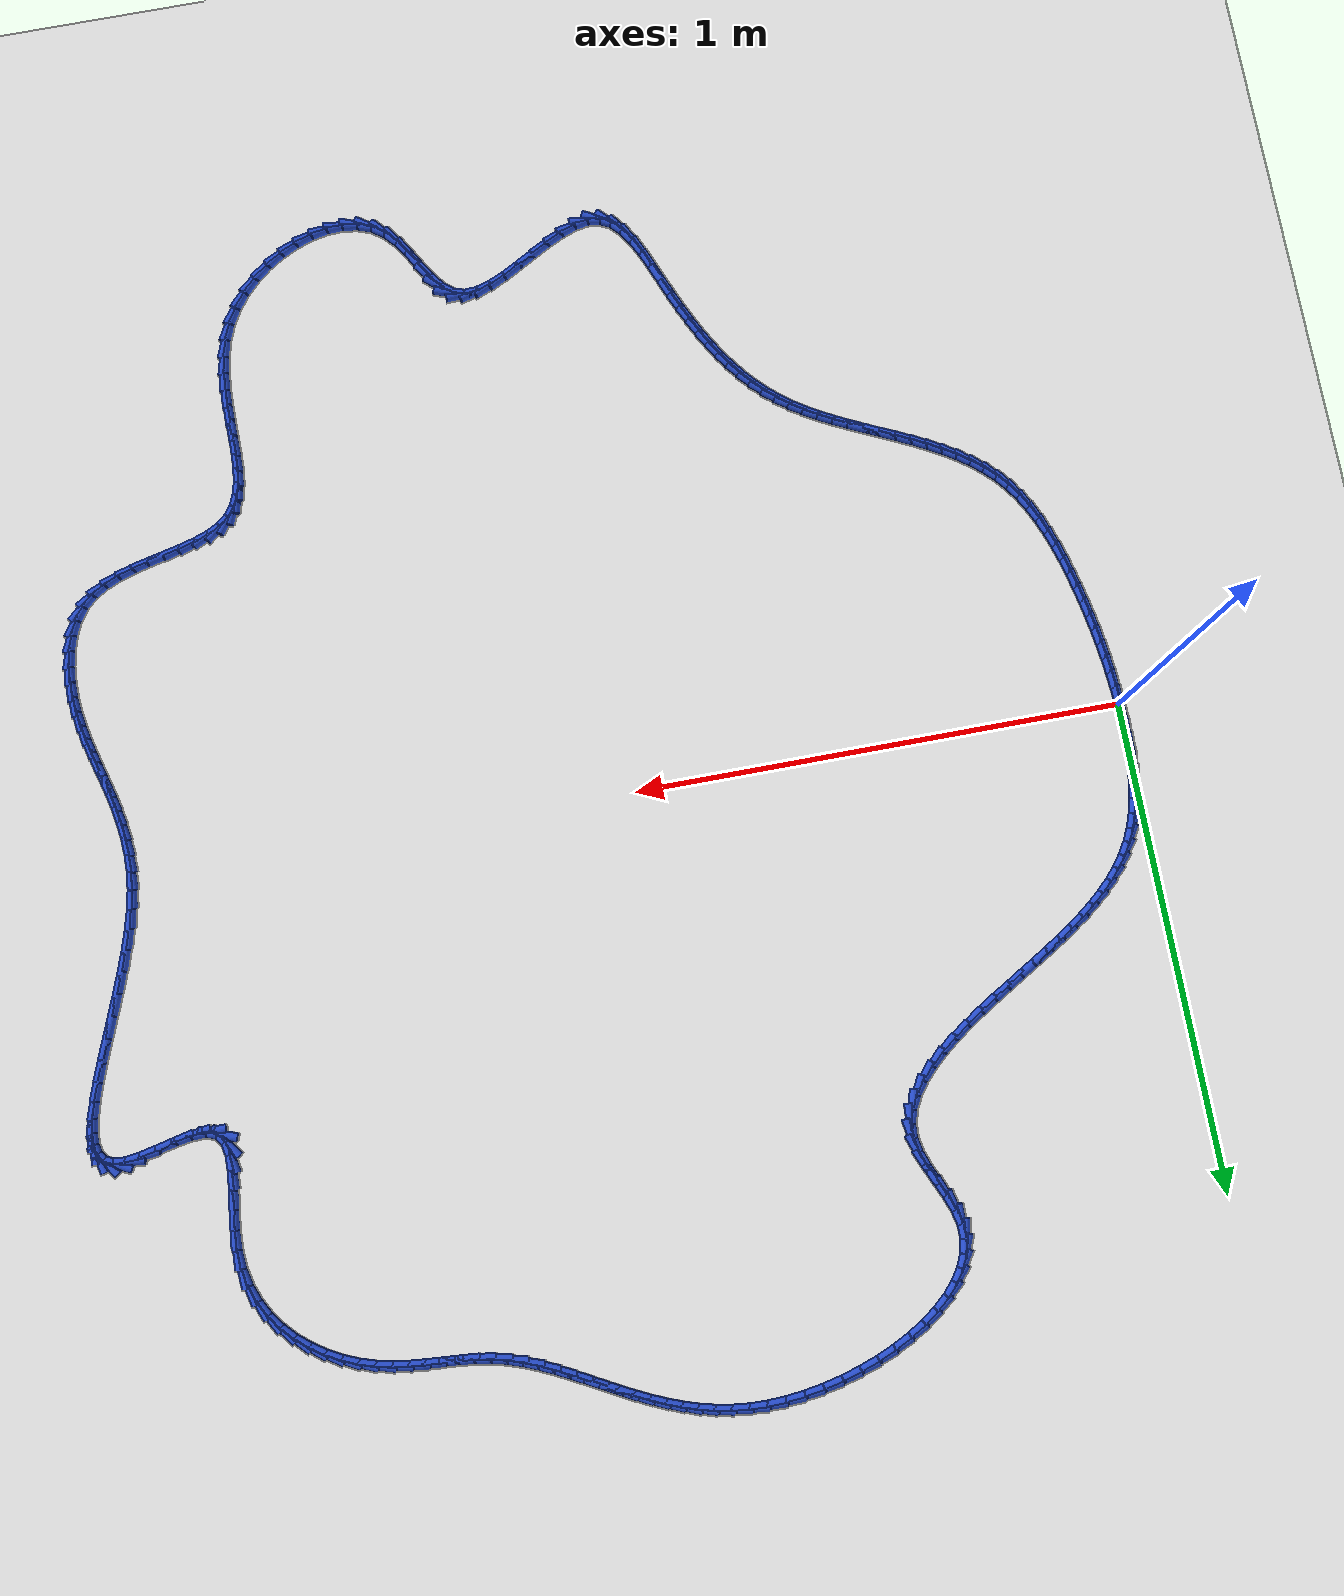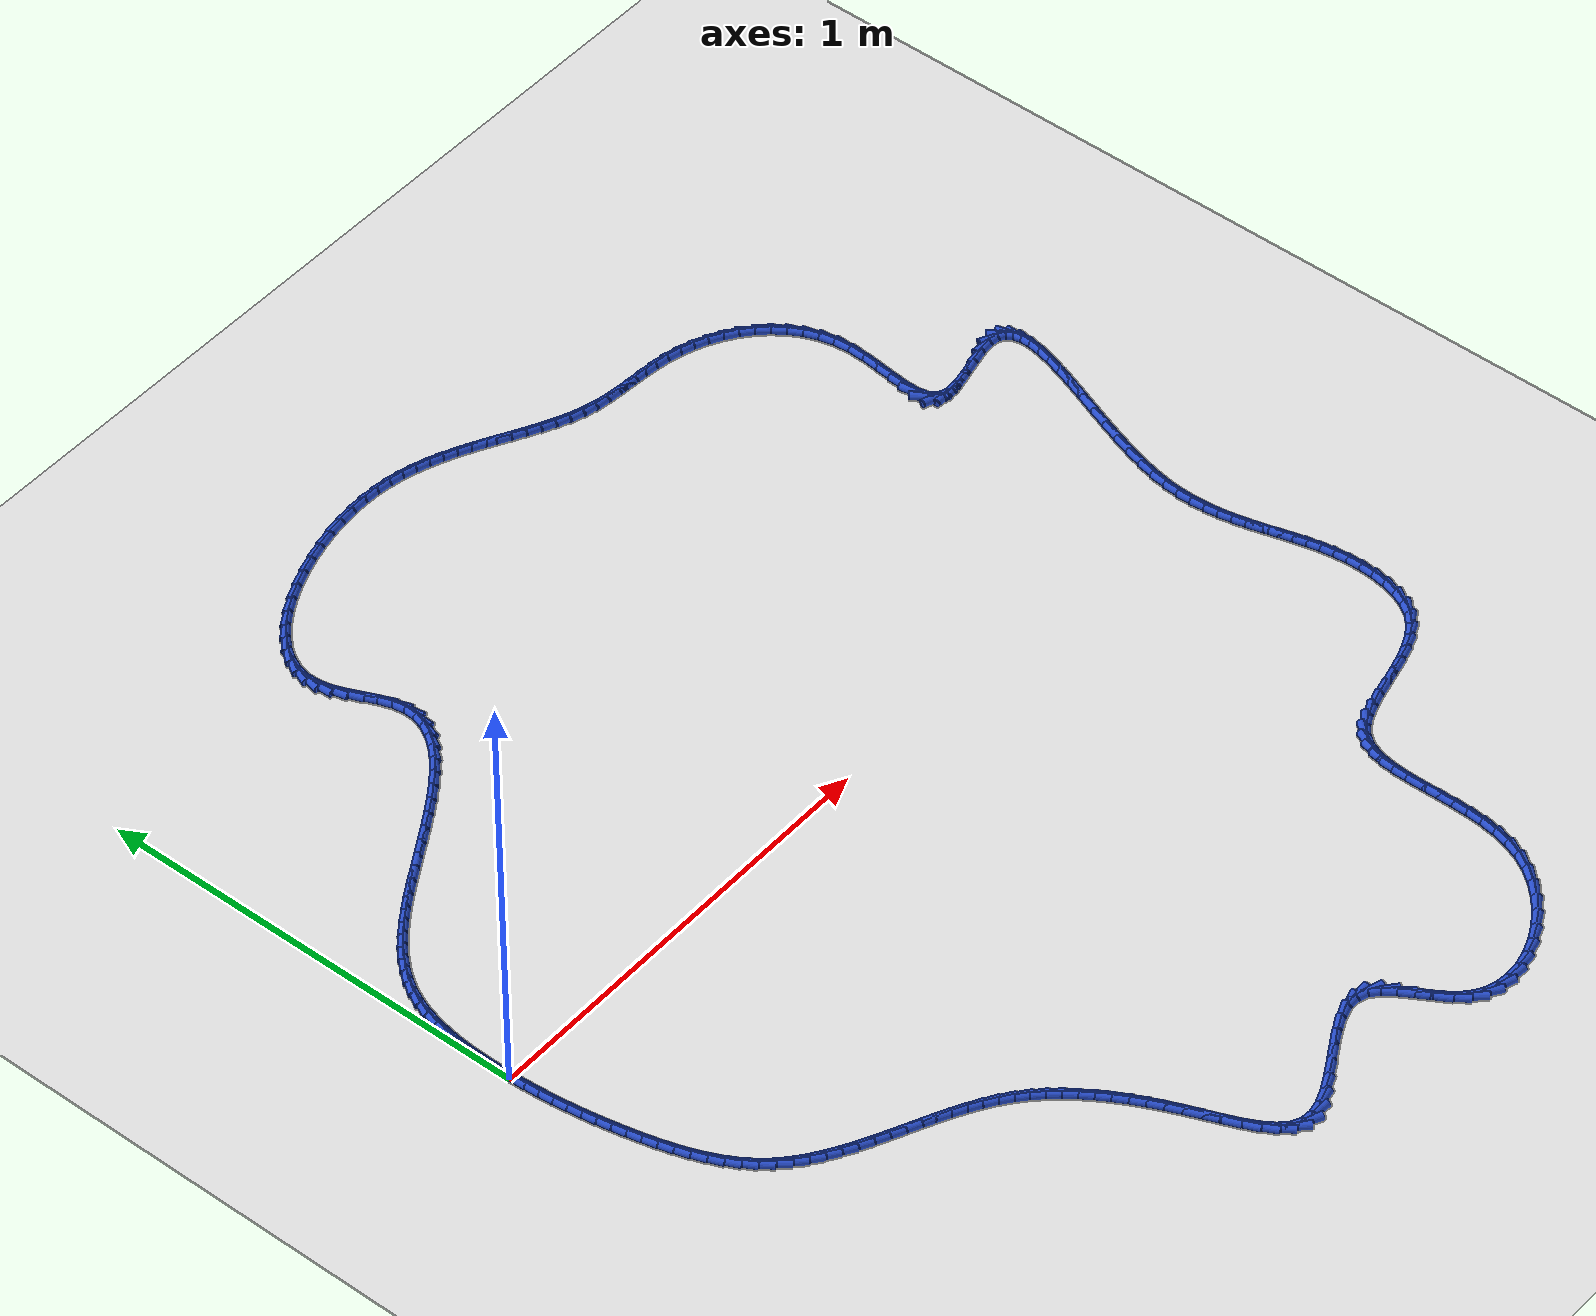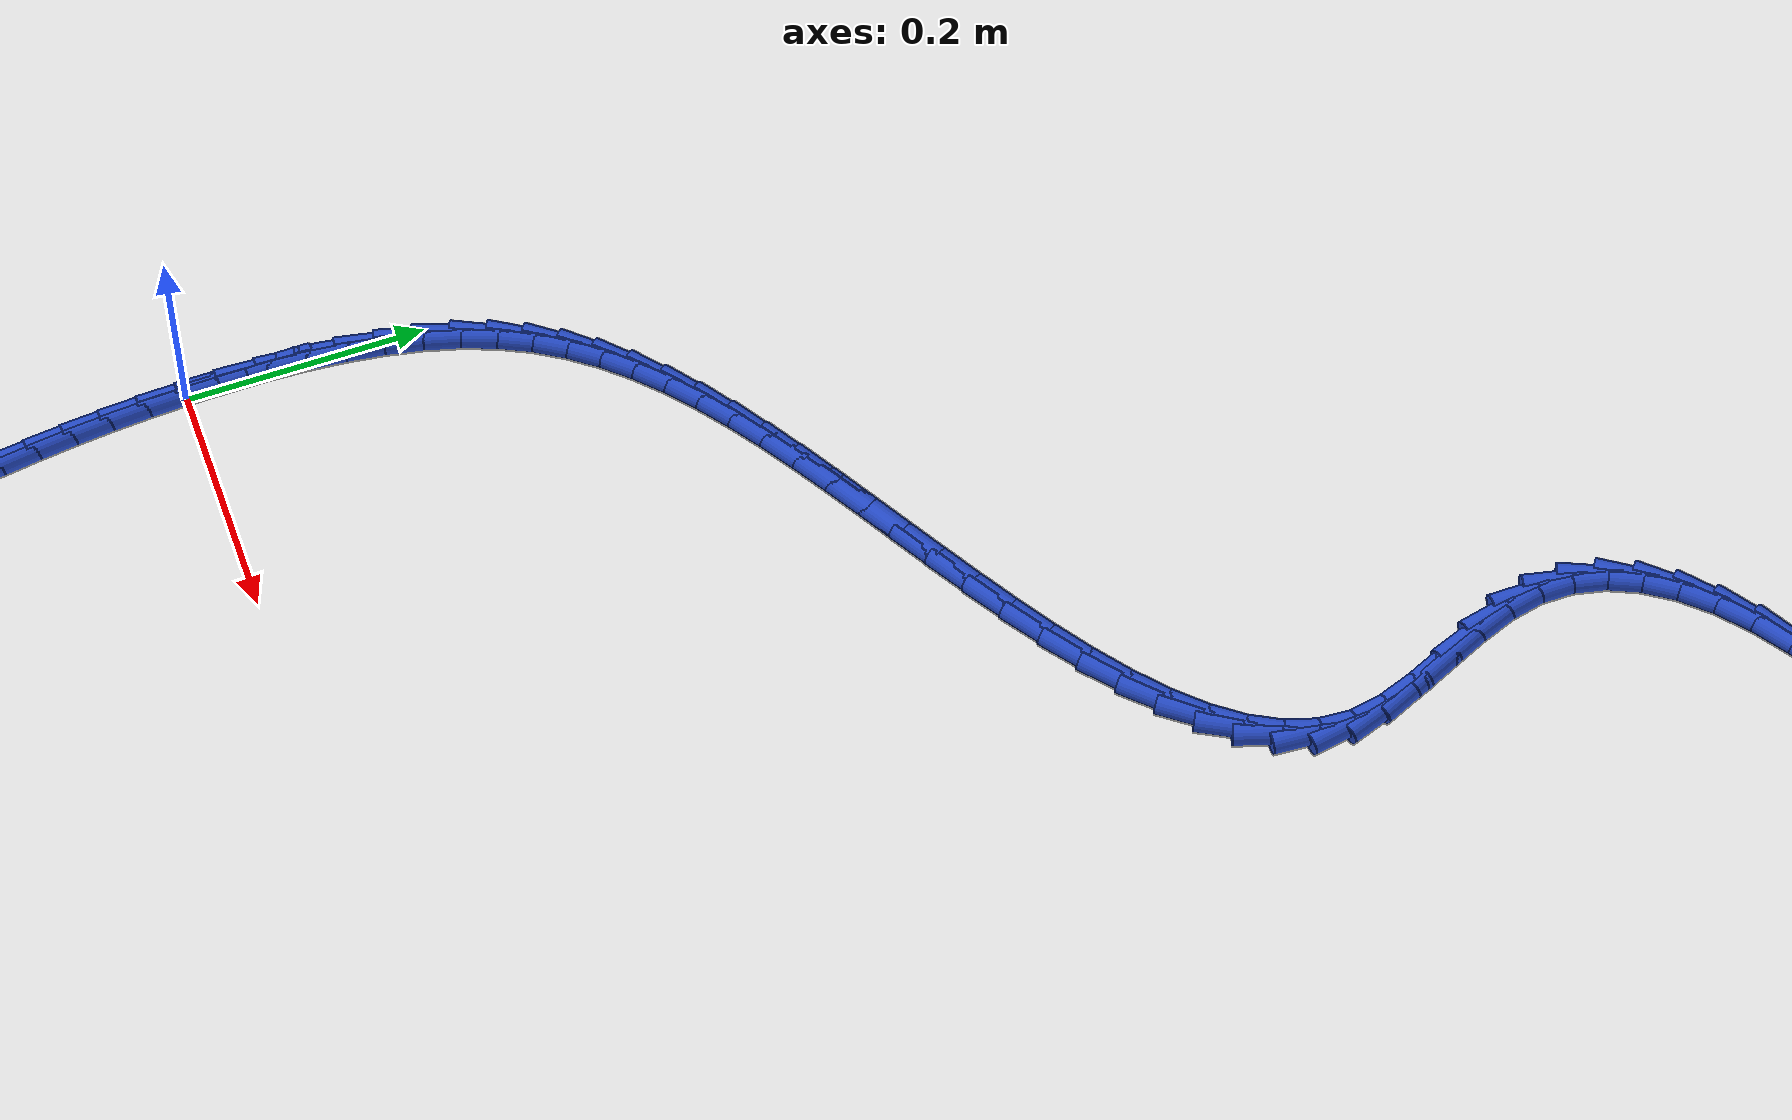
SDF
<sdf version="1.6">
 <world name="default">
  <light name="sun" type="directional">
   <pose>0 0 10 0 -0 0</pose>
   <diffuse>0.8 0.8 0.8 1</diffuse>
   <specular>0.2 0.2 0.2 1</specular>
   <attenuation>
    <range>1000</range>
    <constant>0.9</constant>
    <linear>0.01</linear>
    <quadratic>0.001</quadratic>
   </attenuation>
   <direction>-0.5 0.1 -0.9</direction>
  </light>
  <model name="ground_plane">
   <static>1</static>
   <link name="link">
    <collision name="collision">
     <geometry><plane><normal>0 0 1</normal><size>100 100</size></plane></geometry>
     <surface><friction><ode><mu>100</mu><mu2>50</mu2></ode></friction></surface>
    </collision>
    <visual name="visual">
     <cast_shadows>0</cast_shadows>
     <geometry><plane><normal>0 0 1</normal><size>100 100</size></plane></geometry>
     <material>
      <script><uri>file://media/materials/scripts/gazebo.material</uri><name>Gazebo/WhiteGlow</name></script>
     </material>
    </visual>
   </link>
  </model>
  <gravity>0 0 -9.8</gravity>
  <magnetic_field>6e-06 2.3e-05 -4.2e-05</magnetic_field>
  <atmosphere type="adiabatic"/>
  <physics name="default_physics" default="0" type="ode">
   <max_step_size>0.001</max_step_size>
   <real_time_factor>1</real_time_factor>
   <real_time_update_rate>1000</real_time_update_rate>
  </physics>
  <scene><ambient>0.4 0.4 0.4 1</ambient><background>0.7 0.7 0.7 1</background><shadows>1</shadows></scene>
  <spherical_coordinates>
   <surface_model>EARTH_WGS84</surface_model>
   <latitude_deg>0</latitude_deg>
   <longitude_deg>0</longitude_deg>
   <elevation>0</elevation>
   <heading_deg>0</heading_deg>
  </spherical_coordinates>
  <model name="line">
   <link name="link_0">
    <pose>1.0625181290357943e-17 7.632783294297951e-17 0.01 0 1.57 -1.5450315939455772</pose>
    <collision name="collision">
     <geometry><cylinder><radius>0.01</radius><length>0.08</length></cylinder></geometry>
    </collision>
    <visual name="visual">
     <material>
      <script><name>Gazebo/Blue</name><uri>file://media/materials/scripts/gazebo.material</uri></script>
     </material>
     <geometry><cylinder><radius>0.01</radius><length>0.08</length></cylinder></geometry>
    </visual>
   </link>
   <link name="link_1">
    <pose>-0.0008484708974147878 0.032924197183430516 0.01 0 1.57 1.5680683495373235</pose>
    <collision name="collision">
     <geometry><cylinder><radius>0.01</radius><length>0.08</length></cylinder></geometry>
    </collision>
    <visual name="visual">
     <material>
      <script><name>Gazebo/Blue</name><uri>file://media/materials/scripts/gazebo.material</uri></script>
     </material>
     <geometry><cylinder><radius>0.01</radius><length>0.08</length></cylinder></geometry>
    </visual>
   </link>
   <link name="link_2">
    <pose>-0.0007579796227774928 0.0660956797944067 0.01 0 1.57 1.5330769587160282</pose>
    <collision name="collision">
     <geometry><cylinder><radius>0.01</radius><length>0.08</length></cylinder></geometry>
    </collision>
    <visual name="visual">
     <material>
      <script><name>Gazebo/Blue</name><uri>file://media/materials/scripts/gazebo.material</uri></script>
     </material>
     <geometry><cylinder><radius>0.01</radius><length>0.08</length></cylinder></geometry>
    </visual>
   </link>
   <link name="link_3">
    <pose>0.0004919246648883151 0.09921689914808471 0.01 0 1.57 1.4907269644413075</pose>
    <collision name="collision">
     <geometry><cylinder><radius>0.01</radius><length>0.08</length></cylinder></geometry>
    </collision>
    <visual name="visual">
     <material>
      <script><name>Gazebo/Blue</name><uri>file://media/materials/scripts/gazebo.material</uri></script>
     </material>
     <geometry><cylinder><radius>0.01</radius><length>0.08</length></cylinder></geometry>
    </visual>
   </link>
   <link name="link_4">
    <pose>0.0031216928065590597 0.13199030655962074 0.01 0 1.57 1.439886070392241</pose>
    <collision name="collision">
     <geometry><cylinder><radius>0.01</radius><length>0.08</length></cylinder></geometry>
    </collision>
    <visual name="visual">
     <material>
      <script><name>Gazebo/Blue</name><uri>file://media/materials/scripts/gazebo.material</uri></script>
     </material>
     <geometry><cylinder><radius>0.01</radius><length>0.08</length></cylinder></geometry>
    </visual>
   </link>
   <link name="link_5">
    <pose>0.007351775643211166 0.1641183533441709 0.01 0 1.57 1.3791478052844761</pose>
    <collision name="collision">
     <geometry><cylinder><radius>0.01</radius><length>0.08</length></cylinder></geometry>
    </collision>
    <visual name="visual">
     <material>
      <script><name>Gazebo/Blue</name><uri>file://media/materials/scripts/gazebo.material</uri></script>
     </material>
     <geometry><cylinder><radius>0.01</radius><length>0.08</length></cylinder></geometry>
    </visual>
   </link>
   <link name="link_6">
    <pose>0.013402624015821053 0.19530349081689147 0.01 0 1.57 1.3068665840910743</pose>
    <collision name="collision">
     <geometry><cylinder><radius>0.01</radius><length>0.08</length></cylinder></geometry>
    </collision>
    <visual name="visual">
     <material>
      <script><name>Gazebo/Blue</name><uri>file://media/materials/scripts/gazebo.material</uri></script>
     </material>
     <geometry><cylinder><radius>0.01</radius><length>0.08</length></cylinder></geometry>
    </visual>
   </link>
   <link name="link_7">
    <pose>0.021494688765365148 0.22524817029293834 0.01 0 1.57 1.221278306727714</pose>
    <collision name="collision">
     <geometry><cylinder><radius>0.01</radius><length>0.08</length></cylinder></geometry>
    </collision>
    <visual name="visual">
     <material>
      <script><name>Gazebo/Blue</name><uri>file://media/materials/scripts/gazebo.material</uri></script>
     </material>
     <geometry><cylinder><radius>0.01</radius><length>0.08</length></cylinder></geometry>
    </visual>
   </link>
   <link name="link_8">
    <pose>0.031848420732819856 0.2536548430874677 0.01 0 1.57 1.122448645617586</pose>
    <collision name="collision">
     <geometry><cylinder><radius>0.01</radius><length>0.08</length></cylinder></geometry>
    </collision>
    <visual name="visual">
     <material>
      <script><name>Gazebo/Blue</name><uri>file://media/materials/scripts/gazebo.material</uri></script>
     </material>
     <geometry><cylinder><radius>0.01</radius><length>0.08</length></cylinder></geometry>
    </visual>
   </link>
   <link name="link_9">
    <pose>0.044650600942844926 0.2802695613152772 0.01 0 1.57 1.0224471368903416</pose>
    <collision name="collision">
     <geometry><cylinder><radius>0.01</radius><length>0.08</length></cylinder></geometry>
    </collision>
    <visual name="visual">
     <material>
      <script><name>Gazebo/Blue</name><uri>file://media/materials/scripts/gazebo.material</uri></script>
     </material>
     <geometry><cylinder><radius>0.01</radius><length>0.08</length></cylinder></geometry>
    </visual>
   </link>
   <link name="link_10">
    <pose>0.05984798389931778 0.30514919994041223 0.01 0 1.57 0.9291403538744517</pose>
    <collision name="collision">
     <geometry><cylinder><radius>0.01</radius><length>0.08</length></cylinder></geometry>
    </collision>
    <visual name="visual">
     <material>
      <script><name>Gazebo/Blue</name><uri>file://media/materials/scripts/gazebo.material</uri></script>
     </material>
     <geometry><cylinder><radius>0.01</radius><length>0.08</length></cylinder></geometry>
    </visual>
   </link>
   <link name="link_11">
    <pose>0.07728309836895332 0.3284856012650455 0.01 0 1.57 0.8448598932030486</pose>
    <collision name="collision">
     <geometry><cylinder><radius>0.01</radius><length>0.08</length></cylinder></geometry>
    </collision>
    <visual name="visual">
     <material>
      <script><name>Gazebo/Blue</name><uri>file://media/materials/scripts/gazebo.material</uri></script>
     </material>
     <geometry><cylinder><radius>0.01</radius><length>0.08</length></cylinder></geometry>
    </visual>
   </link>
   <link name="link_12">
    <pose>0.09679804924913331 0.3504711564818364 0.01 0 1.57 0.7709709987590738</pose>
    <collision name="collision">
     <geometry><cylinder><radius>0.01</radius><length>0.08</length></cylinder></geometry>
    </collision>
    <visual name="visual">
     <material>
      <script><name>Gazebo/Blue</name><uri>file://media/materials/scripts/gazebo.material</uri></script>
     </material>
     <geometry><cylinder><radius>0.01</radius><length>0.08</length></cylinder></geometry>
    </visual>
   </link>
   <link name="link_13">
    <pose>0.11823494143723934 0.3712982567834442 0.01 0 1.57 0.7079927795087475</pose>
    <collision name="collision">
     <geometry><cylinder><radius>0.01</radius><length>0.08</length></cylinder></geometry>
    </collision>
    <visual name="visual">
     <material>
      <script><name>Gazebo/Blue</name><uri>file://media/materials/scripts/gazebo.material</uri></script>
     </material>
     <geometry><cylinder><radius>0.01</radius><length>0.08</length></cylinder></geometry>
    </visual>
   </link>
   <link name="link_14">
    <pose>0.14143587983065312 0.39115929336252836 0.01 0 1.57 0.6558219254184303</pose>
    <collision name="collision">
     <geometry><cylinder><radius>0.01</radius><length>0.08</length></cylinder></geometry>
    </collision>
    <visual name="visual">
     <material>
      <script><name>Gazebo/Blue</name><uri>file://media/materials/scripts/gazebo.material</uri></script>
     </material>
     <geometry><cylinder><radius>0.01</radius><length>0.08</length></cylinder></geometry>
    </visual>
   </link>
   <link name="link_15">
    <pose>0.1662429693267564 0.4102466574117484 0.01 0 1.57 0.6139736487818335</pose>
    <collision name="collision">
     <geometry><cylinder><radius>0.01</radius><length>0.08</length></cylinder></geometry>
    </collision>
    <visual name="visual">
     <material>
      <script><name>Gazebo/Blue</name><uri>file://media/materials/scripts/gazebo.material</uri></script>
     </material>
     <geometry><cylinder><radius>0.01</radius><length>0.08</length></cylinder></geometry>
    </visual>
   </link>
   <link name="link_16">
    <pose>0.1924983148229308 0.42875274012376374 0.01 0 1.57 0.581778861898263</pose>
    <collision name="collision">
     <geometry><cylinder><radius>0.01</radius><length>0.08</length></cylinder></geometry>
    </collision>
    <visual name="visual">
     <material>
      <script><name>Gazebo/Blue</name><uri>file://media/materials/scripts/gazebo.material</uri></script>
     </material>
     <geometry><cylinder><radius>0.01</radius><length>0.08</length></cylinder></geometry>
    </visual>
   </link>
   <link name="link_17">
    <pose>0.2200440212165581 0.4468699326912337 0.01 0 1.57 0.5585199745004578</pose>
    <collision name="collision">
     <geometry><cylinder><radius>0.01</radius><length>0.08</length></cylinder></geometry>
    </collision>
    <visual name="visual">
     <material>
      <script><name>Gazebo/Blue</name><uri>file://media/materials/scripts/gazebo.material</uri></script>
     </material>
     <geometry><cylinder><radius>0.01</radius><length>0.08</length></cylinder></geometry>
    </visual>
   </link>
   <link name="link_18">
    <pose>0.24872219340501994 0.4647906263068178 0.01 0 1.57 0.5435118615986578</pose>
    <collision name="collision">
     <geometry><cylinder><radius>0.01</radius><length>0.08</length></cylinder></geometry>
    </collision>
    <visual name="visual">
     <material>
      <script><name>Gazebo/Blue</name><uri>file://media/materials/scripts/gazebo.material</uri></script>
     </material>
     <geometry><cylinder><radius>0.01</radius><length>0.08</length></cylinder></geometry>
    </visual>
   </link>
   <link name="link_19">
    <pose>0.2783749362856981 0.48270721216317536 0.01 0 1.57 0.5361424447199818</pose>
    <collision name="collision">
     <geometry><cylinder><radius>0.01</radius><length>0.08</length></cylinder></geometry>
    </collision>
    <visual name="visual">
     <material>
      <script><name>Gazebo/Blue</name><uri>file://media/materials/scripts/gazebo.material</uri></script>
     </material>
     <geometry><cylinder><radius>0.01</radius><length>0.08</length></cylinder></geometry>
    </visual>
   </link>
   <link name="link_20">
    <pose>0.3088443547559741 0.500812081452966 0.01 0 1.57 0.5358866651339143</pose>
    <collision name="collision">
     <geometry><cylinder><radius>0.01</radius><length>0.08</length></cylinder></geometry>
    </collision>
    <visual name="visual">
     <material>
      <script><name>Gazebo/Blue</name><uri>file://media/materials/scripts/gazebo.material</uri></script>
     </material>
     <geometry><cylinder><radius>0.01</radius><length>0.08</length></cylinder></geometry>
    </visual>
   </link>
   <link name="link_21">
    <pose>0.33997255371323 0.5192976253688489 0.01 0 1.57 0.5423041037000075</pose>
    <collision name="collision">
     <geometry><cylinder><radius>0.01</radius><length>0.08</length></cylinder></geometry>
    </collision>
    <visual name="visual">
     <material>
      <script><name>Gazebo/Blue</name><uri>file://media/materials/scripts/gazebo.material</uri></script>
     </material>
     <geometry><cylinder><radius>0.01</radius><length>0.08</length></cylinder></geometry>
    </visual>
   </link>
   <link name="link_22">
    <pose>0.3716016380548469 0.5383562351034835 0.01 0 1.57 0.5552104559346642</pose>
    <collision name="collision">
     <geometry><cylinder><radius>0.01</radius><length>0.08</length></cylinder></geometry>
    </collision>
    <visual name="visual">
     <material>
      <script><name>Gazebo/Blue</name><uri>file://media/materials/scripts/gazebo.material</uri></script>
     </material>
     <geometry><cylinder><radius>0.01</radius><length>0.08</length></cylinder></geometry>
    </visual>
   </link>
   <link name="link_23">
    <pose>0.4035504675887567 0.5581740081163631 0.01 0 1.57 0.5771610278812183</pose>
    <collision name="collision">
     <geometry><cylinder><radius>0.01</radius><length>0.08</length></cylinder></geometry>
    </collision>
    <visual name="visual">
     <material>
      <script><name>Gazebo/Blue</name><uri>file://media/materials/scripts/gazebo.material</uri></script>
     </material>
     <geometry><cylinder><radius>0.01</radius><length>0.08</length></cylinder></geometry>
    </visual>
   </link>
   <link name="link_24">
    <pose>0.4352969522460977 0.5788447278514872 0.01 0 1.57 0.6110136186493721</pose>
    <collision name="collision">
     <geometry><cylinder><radius>0.01</radius><length>0.08</length></cylinder></geometry>
    </collision>
    <visual name="visual">
     <material>
      <script><name>Gazebo/Blue</name><uri>file://media/materials/scripts/gazebo.material</uri></script>
     </material>
     <geometry><cylinder><radius>0.01</radius><length>0.08</length></cylinder></geometry>
    </visual>
   </link>
   <link name="link_25">
    <pose>0.46606000570500145 0.6003920531224032 0.01 0 1.57 0.6588139061211348</pose>
    <collision name="collision">
     <geometry><cylinder><radius>0.01</radius><length>0.08</length></cylinder></geometry>
    </collision>
    <visual name="visual">
     <material>
      <script><name>Gazebo/Blue</name><uri>file://media/materials/scripts/gazebo.material</uri></script>
     </material>
     <geometry><cylinder><radius>0.01</radius><length>0.08</length></cylinder></geometry>
    </visual>
   </link>
   <link name="link_26">
    <pose>0.49505207661092077 0.6228378923002408 0.01 0 1.57 0.723883744061787</pose>
    <collision name="collision">
     <geometry><cylinder><radius>0.01</radius><length>0.08</length></cylinder></geometry>
    </collision>
    <visual name="visual">
     <material>
      <script><name>Gazebo/Blue</name><uri>file://media/materials/scripts/gazebo.material</uri></script>
     </material>
     <geometry><cylinder><radius>0.01</radius><length>0.08</length></cylinder></geometry>
    </visual>
   </link>
   <link name="link_27">
    <pose>0.5214856136093086 0.6462041537561292 0.01 0 1.57 0.8111570701258786</pose>
    <collision name="collision">
     <geometry><cylinder><radius>0.01</radius><length>0.08</length></cylinder></geometry>
    </collision>
    <visual name="visual">
     <material>
      <script><name>Gazebo/Blue</name><uri>file://media/materials/scripts/gazebo.material</uri></script>
     </material>
     <geometry><cylinder><radius>0.01</radius><length>0.08</length></cylinder></geometry>
    </visual>
   </link>
   <link name="link_28">
    <pose>0.5445730653456173 0.6705127458611976 0.01 0 1.57 0.9273156854958221</pose>
    <collision name="collision">
     <geometry><cylinder><radius>0.01</radius><length>0.08</length></cylinder></geometry>
    </collision>
    <visual name="visual">
     <material>
      <script><name>Gazebo/Blue</name><uri>file://media/materials/scripts/gazebo.material</uri></script>
     </material>
     <geometry><cylinder><radius>0.01</radius><length>0.08</length></cylinder></geometry>
    </visual>
   </link>
   <link name="link_29">
    <pose>0.5635268804652999 0.6957855769865753 0.01 0 1.57 1.0800139831547968</pose>
    <collision name="collision">
     <geometry><cylinder><radius>0.01</radius><length>0.08</length></cylinder></geometry>
    </collision>
    <visual name="visual">
     <material>
      <script><name>Gazebo/Blue</name><uri>file://media/materials/scripts/gazebo.material</uri></script>
     </material>
     <geometry><cylinder><radius>0.01</radius><length>0.08</length></cylinder></geometry>
    </visual>
   </link>
   <link name="link_30">
    <pose>0.5775595076138088 0.7220445555033914 0.01 0 1.57 1.2745090172132927</pose>
    <collision name="collision">
     <geometry><cylinder><radius>0.01</radius><length>0.08</length></cylinder></geometry>
    </collision>
    <visual name="visual">
     <material>
      <script><name>Gazebo/Blue</name><uri>file://media/materials/scripts/gazebo.material</uri></script>
     </material>
     <geometry><cylinder><radius>0.01</radius><length>0.08</length></cylinder></geometry>
    </visual>
   </link>
   <link name="link_31">
    <pose>0.5858833954365971 0.7493115897827752 0.01 0 1.57 1.506299652841662</pose>
    <collision name="collision">
     <geometry><cylinder><radius>0.01</radius><length>0.08</length></cylinder></geometry>
    </collision>
    <visual name="visual">
     <material>
      <script><name>Gazebo/Blue</name><uri>file://media/materials/scripts/gazebo.material</uri></script>
     </material>
     <geometry><cylinder><radius>0.01</radius><length>0.08</length></cylinder></geometry>
    </visual>
   </link>
   <link name="link_32">
    <pose>0.587710992579117 0.7776085881958563 0.01 0 1.57 -1.396954214097311</pose>
    <collision name="collision">
     <geometry><cylinder><radius>0.01</radius><length>0.08</length></cylinder></geometry>
    </collision>
    <visual name="visual">
     <material>
      <script><name>Gazebo/Blue</name><uri>file://media/materials/scripts/gazebo.material</uri></script>
     </material>
     <geometry><cylinder><radius>0.01</radius><length>0.08</length></cylinder></geometry>
    </visual>
   </link>
   <link name="link_33">
    <pose>0.5825631102042446 0.8069220803345428 0.01 0 1.57 -1.2353781585562915</pose>
    <collision name="collision">
     <geometry><cylinder><radius>0.01</radius><length>0.08</length></cylinder></geometry>
    </collision>
    <visual name="visual">
     <material>
      <script><name>Gazebo/Blue</name><uri>file://media/materials/scripts/gazebo.material</uri></script>
     </material>
     <geometry><cylinder><radius>0.01</radius><length>0.08</length></cylinder></geometry>
    </visual>
   </link>
   <link name="link_34">
    <pose>0.5720798337416726 0.8369954490651901 0.01 0 1.57 -1.1596192470447129</pose>
    <collision name="collision">
     <geometry><cylinder><radius>0.01</radius><length>0.08</length></cylinder></geometry>
    </collision>
    <visual name="visual">
     <material>
      <script><name>Gazebo/Blue</name><uri>file://media/materials/scripts/gazebo.material</uri></script>
     </material>
     <geometry><cylinder><radius>0.01</radius><length>0.08</length></cylinder></geometry>
    </visual>
   </link>
   <link name="link_35">
    <pose>0.5587920275016804 0.867469877189067 0.01 0 1.57 -1.1526928461941084</pose>
    <collision name="collision">
     <geometry><cylinder><radius>0.01</radius><length>0.08</length></cylinder></geometry>
    </collision>
    <visual name="visual">
     <material>
      <script><name>Gazebo/Blue</name><uri>file://media/materials/scripts/gazebo.material</uri></script>
     </material>
     <geometry><cylinder><radius>0.01</radius><length>0.08</length></cylinder></geometry>
    </visual>
   </link>
   <link name="link_36">
    <pose>0.5452336360803327 0.8979861941027811 0.01 0 1.57 -1.2128854338016268</pose>
    <collision name="collision">
     <geometry><cylinder><radius>0.01</radius><length>0.08</length></cylinder></geometry>
    </collision>
    <visual name="visual">
     <material>
      <script><name>Gazebo/Blue</name><uri>file://media/materials/scripts/gazebo.material</uri></script>
     </material>
     <geometry><cylinder><radius>0.01</radius><length>0.08</length></cylinder></geometry>
    </visual>
   </link>
   <link name="link_37">
    <pose>0.533938604073693 0.9281852292029413 0.01 0 1.57 -1.353946783003777</pose>
    <collision name="collision">
     <geometry><cylinder><radius>0.01</radius><length>0.08</length></cylinder></geometry>
    </collision>
    <visual name="visual">
     <material>
      <script><name>Gazebo/Blue</name><uri>file://media/materials/scripts/gazebo.material</uri></script>
     </material>
     <geometry><cylinder><radius>0.01</radius><length>0.08</length></cylinder></geometry>
    </visual>
   </link>
   <link name="link_38">
    <pose>0.5274342516827468 0.95770836431507 0.01 0 1.57 -1.5666409314998242</pose>
    <collision name="collision">
     <geometry><cylinder><radius>0.01</radius><length>0.08</length></cylinder></geometry>
    </collision>
    <visual name="visual">
     <material>
      <script><name>Gazebo/Blue</name><uri>file://media/materials/scripts/gazebo.material</uri></script>
     </material>
     <geometry><cylinder><radius>0.01</radius><length>0.08</length></cylinder></geometry>
    </visual>
   </link>
   <link name="link_39">
    <pose>0.5273155464452515 0.9862747330538709 0.01 0 1.57 1.3567034762428667</pose>
    <collision name="collision">
     <geometry><cylinder><radius>0.01</radius><length>0.08</length></cylinder></geometry>
    </collision>
    <visual name="visual">
     <material>
      <script><name>Gazebo/Blue</name><uri>file://media/materials/scripts/gazebo.material</uri></script>
     </material>
     <geometry><cylinder><radius>0.01</radius><length>0.08</length></cylinder></geometry>
    </visual>
   </link>
   <link name="link_40">
    <pose>0.5332916888896341 1.0137607290116697 0.01 0 1.57 1.1569189082040678</pose>
    <collision name="collision">
     <geometry><cylinder><radius>0.01</radius><length>0.08</length></cylinder></geometry>
    </collision>
    <visual name="visual">
     <material>
      <script><name>Gazebo/Blue</name><uri>file://media/materials/scripts/gazebo.material</uri></script>
     </material>
     <geometry><cylinder><radius>0.01</radius><length>0.08</length></cylinder></geometry>
    </visual>
   </link>
   <link name="link_41">
    <pose>0.5448443693371267 1.0400617185647665 0.01 0 1.57 0.984548570773763</pose>
    <collision name="collision">
     <geometry><cylinder><radius>0.01</radius><length>0.08</length></cylinder></geometry>
    </collision>
    <visual name="visual">
     <material>
      <script><name>Gazebo/Blue</name><uri>file://media/materials/scripts/gazebo.material</uri></script>
     </material>
     <geometry><cylinder><radius>0.01</radius><length>0.08</length></cylinder></geometry>
    </visual>
   </link>
   <link name="link_42">
    <pose>0.5614552781089603 1.0650730680894596 0.01 0 1.57 0.8404321920779939</pose>
    <collision name="collision">
     <geometry><cylinder><radius>0.01</radius><length>0.08</length></cylinder></geometry>
    </collision>
    <visual name="visual">
     <material>
      <script><name>Gazebo/Blue</name><uri>file://media/materials/scripts/gazebo.material</uri></script>
     </material>
     <geometry><cylinder><radius>0.01</radius><length>0.08</length></cylinder></geometry>
    </visual>
   </link>
   <link name="link_43">
    <pose>0.5826061055263669 1.0886901439620487 0.01 0 1.57 0.7209026531881378</pose>
    <collision name="collision">
     <geometry><cylinder><radius>0.01</radius><length>0.08</length></cylinder></geometry>
    </collision>
    <visual name="visual">
     <material>
      <script><name>Gazebo/Blue</name><uri>file://media/materials/scripts/gazebo.material</uri></script>
     </material>
     <geometry><cylinder><radius>0.01</radius><length>0.08</length></cylinder></geometry>
    </visual>
   </link>
   <link name="link_44">
    <pose>0.6077785419105778 1.1108083125588326 0.01 0 1.57 0.6209870825993028</pose>
    <collision name="collision">
     <geometry><cylinder><radius>0.01</radius><length>0.08</length></cylinder></geometry>
    </collision>
    <visual name="visual">
     <material>
      <script><name>Gazebo/Blue</name><uri>file://media/materials/scripts/gazebo.material</uri></script>
     </material>
     <geometry><cylinder><radius>0.01</radius><length>0.08</length></cylinder></geometry>
    </visual>
   </link>
   <link name="link_45">
    <pose>0.6364542775828247 1.1313229402561102 0.01 0 1.57 0.5359956433028493</pose>
    <collision name="collision">
     <geometry><cylinder><radius>0.01</radius><length>0.08</length></cylinder></geometry>
    </collision>
    <visual name="visual">
     <material>
      <script><name>Gazebo/Blue</name><uri>file://media/materials/scripts/gazebo.material</uri></script>
     </material>
     <geometry><cylinder><radius>0.01</radius><length>0.08</length></cylinder></geometry>
    </visual>
   </link>
   <link name="link_46">
    <pose>0.6681150028643389 1.1501293934301813 0.01 0 1.57 0.46200400113984075</pose>
    <collision name="collision">
     <geometry><cylinder><radius>0.01</radius><length>0.08</length></cylinder></geometry>
    </collision>
    <visual name="visual">
     <material>
      <script><name>Gazebo/Blue</name><uri>file://media/materials/scripts/gazebo.material</uri></script>
     </material>
     <geometry><cylinder><radius>0.01</radius><length>0.08</length></cylinder></geometry>
    </visual>
   </link>
   <link name="link_47">
    <pose>0.7022424080763523 1.167123038457345 0.01 0 1.57 0.39584477258026385</pose>
    <collision name="collision">
     <geometry><cylinder><radius>0.01</radius><length>0.08</length></cylinder></geometry>
    </collision>
    <visual name="visual">
     <material>
      <script><name>Gazebo/Blue</name><uri>file://media/materials/scripts/gazebo.material</uri></script>
     </material>
     <geometry><cylinder><radius>0.01</radius><length>0.08</length></cylinder></geometry>
    </visual>
   </link>
   <link name="link_48">
    <pose>0.7383181835400964 1.1821992417138998 0.01 0 1.57 0.33494184119309933</pose>
    <collision name="collision">
     <geometry><cylinder><radius>0.01</radius><length>0.08</length></cylinder></geometry>
    </collision>
    <visual name="visual">
     <material>
      <script><name>Gazebo/Blue</name><uri>file://media/materials/scripts/gazebo.material</uri></script>
     </material>
     <geometry><cylinder><radius>0.01</radius><length>0.08</length></cylinder></geometry>
    </visual>
   </link>
   <link name="link_49">
    <pose>0.7758240195768021 1.1952533695761458 0.01 0 1.57 0.2771192331949611</pose>
    <collision name="collision">
     <geometry><cylinder><radius>0.01</radius><length>0.08</length></cylinder></geometry>
    </collision>
    <visual name="visual">
     <material>
      <script><name>Gazebo/Blue</name><uri>file://media/materials/scripts/gazebo.material</uri></script>
     </material>
     <geometry><cylinder><radius>0.01</radius><length>0.08</length></cylinder></geometry>
    </visual>
   </link>
   <link name="link_50">
    <pose>0.8142416065077023 1.206180788420382 0.01 0 1.57 0.2204214518289486</pose>
    <collision name="collision">
     <geometry><cylinder><radius>0.01</radius><length>0.08</length></cylinder></geometry>
    </collision>
    <visual name="visual">
     <material>
      <script><name>Gazebo/Blue</name><uri>file://media/materials/scripts/gazebo.material</uri></script>
     </material>
     <geometry><cylinder><radius>0.01</radius><length>0.08</length></cylinder></geometry>
    </visual>
   </link>
   <link name="link_51">
    <pose>0.853052634654027 1.214876864622907 0.01 0 1.57 0.1629448628683276</pose>
    <collision name="collision">
     <geometry><cylinder><radius>0.01</radius><length>0.08</length></cylinder></geometry>
    </collision>
    <visual name="visual">
     <material>
      <script><name>Gazebo/Blue</name><uri>file://media/materials/scripts/gazebo.material</uri></script>
     </material>
     <geometry><cylinder><radius>0.01</radius><length>0.08</length></cylinder></geometry>
    </visual>
   </link>
   <link name="link_52">
    <pose>0.891738794337009 1.22123696456002 0.01 0 1.57 0.10266570614472696</pose>
    <collision name="collision">
     <geometry><cylinder><radius>0.01</radius><length>0.08</length></cylinder></geometry>
    </collision>
    <visual name="visual">
     <material>
      <script><name>Gazebo/Blue</name><uri>file://media/materials/scripts/gazebo.material</uri></script>
     </material>
     <geometry><cylinder><radius>0.01</radius><length>0.08</length></cylinder></geometry>
    </visual>
   </link>
   <link name="link_53">
    <pose>0.929781775877879 1.225156454608021 0.01 0 1.57 0.03724391091592601</pose>
    <collision name="collision">
     <geometry><cylinder><radius>0.01</radius><length>0.08</length></cylinder></geometry>
    </collision>
    <visual name="visual">
     <material>
      <script><name>Gazebo/Blue</name><uri>file://media/materials/scripts/gazebo.material</uri></script>
     </material>
     <geometry><cylinder><radius>0.01</radius><length>0.08</length></cylinder></geometry>
    </visual>
   </link>
   <link name="link_54">
    <pose>0.9666632695978687 1.2265307011432078 0.01 0 1.57 -0.03509586694153524</pose>
    <collision name="collision">
     <geometry><cylinder><radius>0.01</radius><length>0.08</length></cylinder></geometry>
    </collision>
    <visual name="visual">
     <material>
      <script><name>Gazebo/Blue</name><uri>file://media/materials/scripts/gazebo.material</uri></script>
     </material>
     <geometry><cylinder><radius>0.01</radius><length>0.08</length></cylinder></geometry>
    </visual>
   </link>
   <link name="link_55">
    <pose>1.0019421744516641 1.225292048793278 0.01 0 1.57 -0.10928198007770407</pose>
    <collision name="collision">
     <geometry><cylinder><radius>0.01</radius><length>0.08</length></cylinder></geometry>
    </collision>
    <visual name="visual">
     <material>
      <script><name>Gazebo/Blue</name><uri>file://media/materials/scripts/gazebo.material</uri></script>
     </material>
     <geometry><cylinder><radius>0.01</radius><length>0.08</length></cylinder></geometry>
    </visual>
   </link>
   <link name="link_56">
    <pose>1.0356405928418024 1.2215946885362121 0.01 0 1.57 -0.18118980114431527</pose>
    <collision name="collision">
     <geometry><cylinder><radius>0.01</radius><length>0.08</length></cylinder></geometry>
    </collision>
    <visual name="visual">
     <material>
      <script><name>Gazebo/Blue</name><uri>file://media/materials/scripts/gazebo.material</uri></script>
     </material>
     <geometry><cylinder><radius>0.01</radius><length>0.08</length></cylinder></geometry>
    </visual>
   </link>
   <link name="link_57">
    <pose>1.0679525779578158 1.215675165345199 0.01 0 1.57 -0.24875651099920976</pose>
    <collision name="collision">
     <geometry><cylinder><radius>0.01</radius><length>0.08</length></cylinder></geometry>
    </collision>
    <visual name="visual">
     <material>
      <script><name>Gazebo/Blue</name><uri>file://media/materials/scripts/gazebo.material</uri></script>
     </material>
     <geometry><cylinder><radius>0.01</radius><length>0.08</length></cylinder></geometry>
    </visual>
   </link>
   <link name="link_58">
    <pose>1.099072467121768 1.2077701602756707 0.01 0 1.57 -0.31014629061184196</pose>
    <collision name="collision">
     <geometry><cylinder><radius>0.01</radius><length>0.08</length></cylinder></geometry>
    </collision>
    <visual name="visual">
     <material>
      <script><name>Gazebo/Blue</name><uri>file://media/materials/scripts/gazebo.material</uri></script>
     </material>
     <geometry><cylinder><radius>0.01</radius><length>0.08</length></cylinder></geometry>
    </visual>
   </link>
   <link name="link_59">
    <pose>1.1291945976557205 1.1981163543830604 0.01 0 1.57 -0.36388642734052323</pose>
    <collision name="collision">
     <geometry><cylinder><radius>0.01</radius><length>0.08</length></cylinder></geometry>
    </collision>
    <visual name="visual">
     <material>
      <script><name>Gazebo/Blue</name><uri>file://media/materials/scripts/gazebo.material</uri></script>
     </material>
     <geometry><cylinder><radius>0.01</radius><length>0.08</length></cylinder></geometry>
    </visual>
   </link>
   <link name="link_60">
    <pose>1.1585133068817368 1.1869504287228003 0.01 0 1.57 -0.4089232763050112</pose>
    <collision name="collision">
     <geometry><cylinder><radius>0.01</radius><length>0.08</length></cylinder></geometry>
    </collision>
    <visual name="visual">
     <material>
      <script><name>Gazebo/Blue</name><uri>file://media/materials/scripts/gazebo.material</uri></script>
     </material>
     <geometry><cylinder><radius>0.01</radius><length>0.08</length></cylinder></geometry>
    </visual>
   </link>
   <link name="link_61">
    <pose>1.1872229321218786 1.1745090643503224 0.01 0 1.57 -0.44460271883285246</pose>
    <collision name="collision">
     <geometry><cylinder><radius>0.01</radius><length>0.08</length></cylinder></geometry>
    </collision>
    <visual name="visual">
     <material>
      <script><name>Gazebo/Blue</name><uri>file://media/materials/scripts/gazebo.material</uri></script>
     </material>
     <geometry><cylinder><radius>0.01</radius><length>0.08</length></cylinder></geometry>
    </visual>
   </link>
   <link name="link_62">
    <pose>1.2155178106982085 1.16102894232106 0.01 0 1.57 -0.47060362511649007</pose>
    <collision name="collision">
     <geometry><cylinder><radius>0.01</radius><length>0.08</length></cylinder></geometry>
    </collision>
    <visual name="visual">
     <material>
      <script><name>Gazebo/Blue</name><uri>file://media/materials/scripts/gazebo.material</uri></script>
     </material>
     <geometry><cylinder><radius>0.01</radius><length>0.08</length></cylinder></geometry>
    </visual>
   </link>
   <link name="link_63">
    <pose>1.2435922799327899 1.1467467436904446 0.01 0 1.57 -0.48685586399208586</pose>
    <collision name="collision">
     <geometry><cylinder><radius>0.01</radius><length>0.08</length></cylinder></geometry>
    </collision>
    <visual name="visual">
     <material>
      <script><name>Gazebo/Blue</name><uri>file://media/materials/scripts/gazebo.material</uri></script>
     </material>
     <geometry><cylinder><radius>0.01</radius><length>0.08</length></cylinder></geometry>
    </visual>
   </link>
   <link name="link_64">
    <pose>1.2716406771476843 1.1318991495139095 0.01 0 1.57 -0.49330244291777964</pose>
    <collision name="collision">
     <geometry><cylinder><radius>0.01</radius><length>0.08</length></cylinder></geometry>
    </collision>
    <visual name="visual">
     <material>
      <script><name>Gazebo/Blue</name><uri>file://media/materials/scripts/gazebo.material</uri></script>
     </material>
     <geometry><cylinder><radius>0.01</radius><length>0.08</length></cylinder></geometry>
    </visual>
   </link>
   <link name="link_65">
    <pose>1.2998517276485444 1.1167318267578665 0.01 0 1.57 -0.48777460467968503</pose>
    <collision name="collision">
     <geometry><cylinder><radius>0.01</radius><length>0.08</length></cylinder></geometry>
    </collision>
    <visual name="visual">
     <material>
      <script><name>Gazebo/Blue</name><uri>file://media/materials/scripts/gazebo.material</uri></script>
     </material>
     <geometry><cylinder><radius>0.01</radius><length>0.08</length></cylinder></geometry>
    </visual>
   </link>
   <link name="link_66">
    <pose>1.3283318960715478 1.1016221574442704 0.01 0 1.57 -0.4685803499271244</pose>
    <collision name="collision">
     <geometry><cylinder><radius>0.01</radius><length>0.08</length></cylinder></geometry>
    </collision>
    <visual name="visual">
     <material>
      <script><name>Gazebo/Blue</name><uri>file://media/materials/scripts/gazebo.material</uri></script>
     </material>
     <geometry><cylinder><radius>0.01</radius><length>0.08</length></cylinder></geometry>
    </visual>
   </link>
   <link name="link_67">
    <pose>1.3571251868235479 1.0870475343611745 0.01 0 1.57 -0.4354119637159868</pose>
    <collision name="collision">
     <geometry><cylinder><radius>0.01</radius><length>0.08</length></cylinder></geometry>
    </collision>
    <visual name="visual">
     <material>
      <script><name>Gazebo/Blue</name><uri>file://media/materials/scripts/gazebo.material</uri></script>
     </material>
     <geometry><cylinder><radius>0.01</radius><length>0.08</length></cylinder></geometry>
    </visual>
   </link>
   <link name="link_68">
    <pose>1.3862740467506751 1.0734878442490714 0.01 0 1.57 -0.38766656314834985</pose>
    <collision name="collision">
     <geometry><cylinder><radius>0.01</radius><length>0.08</length></cylinder></geometry>
    </collision>
    <visual name="visual">
     <material>
      <script><name>Gazebo/Blue</name><uri>file://media/materials/scripts/gazebo.material</uri></script>
     </material>
     <geometry><cylinder><radius>0.01</radius><length>0.08</length></cylinder></geometry>
    </visual>
   </link>
   <link name="link_69">
    <pose>1.4158209226990603 1.0614229738484542 0.01 0 1.57 -0.3245806004094552</pose>
    <collision name="collision">
     <geometry><cylinder><radius>0.01</radius><length>0.08</length></cylinder></geometry>
    </collision>
    <visual name="visual">
     <material>
      <script><name>Gazebo/Blue</name><uri>file://media/materials/scripts/gazebo.material</uri></script>
     </material>
     <geometry><cylinder><radius>0.01</radius><length>0.08</length></cylinder></geometry>
    </visual>
   </link>
   <link name="link_70">
    <pose>1.4458082615148342 1.0513328098998154 0.01 0 1.57 -0.24566906801516292</pose>
    <collision name="collision">
     <geometry><cylinder><radius>0.01</radius><length>0.08</length></cylinder></geometry>
    </collision>
    <visual name="visual">
     <material>
      <script><name>Gazebo/Blue</name><uri>file://media/materials/scripts/gazebo.material</uri></script>
     </material>
     <geometry><cylinder><radius>0.01</radius><length>0.08</length></cylinder></geometry>
    </visual>
   </link>
   <link name="link_71">
    <pose>1.476278074529732 1.0436930014944208 0.01 0 1.57 -0.16463551399433787</pose>
    <collision name="collision">
     <geometry><cylinder><radius>0.01</radius><length>0.08</length></cylinder></geometry>
    </collision>
    <visual name="visual">
     <material>
      <script><name>Gazebo/Blue</name><uri>file://media/materials/scripts/gazebo.material</uri></script>
     </material>
     <geometry><cylinder><radius>0.01</radius><length>0.08</length></cylinder></geometry>
    </visual>
   </link>
   <link name="link_72">
    <pose>1.507228360196232 1.0385509428919517 0.01 0 1.57 -0.10761900310513371</pose>
    <collision name="collision">
     <geometry><cylinder><radius>0.01</radius><length>0.08</length></cylinder></geometry>
    </collision>
    <visual name="visual">
     <material>
      <script><name>Gazebo/Blue</name><uri>file://media/materials/scripts/gazebo.material</uri></script>
     </material>
     <geometry><cylinder><radius>0.01</radius><length>0.08</length></cylinder></geometry>
    </visual>
   </link>
   <link name="link_73">
    <pose>1.5385759505619285 1.0351642616829078 0.01 0 1.57 -0.07752485123252725</pose>
    <collision name="collision">
     <geometry><cylinder><radius>0.01</radius><length>0.08</length></cylinder></geometry>
    </collision>
    <visual name="visual">
     <material>
      <script><name>Gazebo/Blue</name><uri>file://media/materials/scripts/gazebo.material</uri></script>
     </material>
     <geometry><cylinder><radius>0.01</radius><length>0.08</length></cylinder></geometry>
    </visual>
   </link>
   <link name="link_74">
    <pose>1.5702289272033598 1.0327054414823718 0.01 0 1.57 -0.07387656196088468</pose>
    <collision name="collision">
     <geometry><cylinder><radius>0.01</radius><length>0.08</length></cylinder></geometry>
    </collision>
    <visual name="visual">
     <material>
      <script><name>Gazebo/Blue</name><uri>file://media/materials/scripts/gazebo.material</uri></script>
     </material>
     <geometry><cylinder><radius>0.01</radius><length>0.08</length></cylinder></geometry>
    </visual>
   </link>
   <link name="link_75">
    <pose>1.6020953716970612 1.0303469659054256 0.01 0 1.57 -0.09616513398276337</pose>
    <collision name="collision">
     <geometry><cylinder><radius>0.01</radius><length>0.08</length></cylinder></geometry>
    </collision>
    <visual name="visual">
     <material>
      <script><name>Gazebo/Blue</name><uri>file://media/materials/scripts/gazebo.material</uri></script>
     </material>
     <geometry><cylinder><radius>0.01</radius><length>0.08</length></cylinder></geometry>
    </visual>
   </link>
   <link name="link_76">
    <pose>1.6340833656195697 1.0272613185671522 0.01 0 1.57 -0.1439285080394191</pose>
    <collision name="collision">
     <geometry><cylinder><radius>0.01</radius><length>0.08</length></cylinder></geometry>
    </collision>
    <visual name="visual">
     <material>
      <script><name>Gazebo/Blue</name><uri>file://media/materials/scripts/gazebo.material</uri></script>
     </material>
     <geometry><cylinder><radius>0.01</radius><length>0.08</length></cylinder></geometry>
    </visual>
   </link>
   <link name="link_77">
    <pose>1.6661009905474229 1.022620983082634 0.01 0 1.57 -0.2162342092251296</pose>
    <collision name="collision">
     <geometry><cylinder><radius>0.01</radius><length>0.08</length></cylinder></geometry>
    </collision>
    <visual name="visual">
     <material>
      <script><name>Gazebo/Blue</name><uri>file://media/materials/scripts/gazebo.material</uri></script>
     </material>
     <geometry><cylinder><radius>0.01</radius><length>0.08</length></cylinder></geometry>
    </visual>
   </link>
   <link name="link_78">
    <pose>1.6980549061627606 1.0156017102722732 0.01 0 1.57 -0.30388142257924067</pose>
    <collision name="collision">
     <geometry><cylinder><radius>0.01</radius><length>0.08</length></cylinder></geometry>
    </collision>
    <visual name="visual">
     <material>
      <script><name>Gazebo/Blue</name><uri>file://media/materials/scripts/gazebo.material</uri></script>
     </material>
     <geometry><cylinder><radius>0.01</radius><length>0.08</length></cylinder></geometry>
    </visual>
   </link>
   <link name="link_79">
    <pose>1.7297251984878268 1.0056700898093363 0.01 0 1.57 -0.393933834168226</pose>
    <collision name="collision">
     <geometry><cylinder><radius>0.01</radius><length>0.08</length></cylinder></geometry>
    </collision>
    <visual name="visual">
     <material>
      <script><name>Gazebo/Blue</name><uri>file://media/materials/scripts/gazebo.material</uri></script>
     </material>
     <geometry><cylinder><radius>0.01</radius><length>0.08</length></cylinder></geometry>
    </visual>
   </link>
   <link name="link_80">
    <pose>1.7606674321297915 0.9928086129445355 0.01 0 1.57 -0.48709947060590697</pose>
    <collision name="collision">
     <geometry><cylinder><radius>0.01</radius><length>0.08</length></cylinder></geometry>
    </collision>
    <visual name="visual">
     <material>
      <script><name>Gazebo/Blue</name><uri>file://media/materials/scripts/gazebo.material</uri></script>
     </material>
     <geometry><cylinder><radius>0.01</radius><length>0.08</length></cylinder></geometry>
    </visual>
   </link>
   <link name="link_81">
    <pose>1.7904141194395657 0.9770527400200343 0.01 0 1.57 -0.5853447303482275</pose>
    <collision name="collision">
     <geometry><cylinder><radius>0.01</radius><length>0.08</length></cylinder></geometry>
    </collision>
    <visual name="visual">
     <material>
      <script><name>Gazebo/Blue</name><uri>file://media/materials/scripts/gazebo.material</uri></script>
     </material>
     <geometry><cylinder><radius>0.01</radius><length>0.08</length></cylinder></geometry>
    </visual>
   </link>
   <link name="link_82">
    <pose>1.8184977727680594 0.9584379313779963 0.01 0 1.57 -0.6904176097751761</pose>
    <collision name="collision">
     <geometry><cylinder><radius>0.01</radius><length>0.08</length></cylinder></geometry>
    </collision>
    <visual name="visual">
     <material>
      <script><name>Gazebo/Blue</name><uri>file://media/materials/scripts/gazebo.material</uri></script>
     </material>
     <geometry><cylinder><radius>0.01</radius><length>0.08</length></cylinder></geometry>
    </visual>
   </link>
   <link name="link_83">
    <pose>1.8444509044661836 0.9369996473605843 0.01 0 1.57 -0.8037052941563629</pose>
    <collision name="collision">
     <geometry><cylinder><radius>0.01</radius><length>0.08</length></cylinder></geometry>
    </collision>
    <visual name="visual">
     <material>
      <script><name>Gazebo/Blue</name><uri>file://media/materials/scripts/gazebo.material</uri></script>
     </material>
     <geometry><cylinder><radius>0.01</radius><length>0.08</length></cylinder></geometry>
    </visual>
   </link>
   <link name="link_84">
    <pose>1.8678060268848482 0.9127733483099614 0.01 0 1.57 -0.9259802816076672</pose>
    <collision name="collision">
     <geometry><cylinder><radius>0.01</radius><length>0.08</length></cylinder></geometry>
    </collision>
    <visual name="visual">
     <material>
      <script><name>Gazebo/Blue</name><uri>file://media/materials/scripts/gazebo.material</uri></script>
     </material>
     <geometry><cylinder><radius>0.01</radius><length>0.08</length></cylinder></geometry>
    </visual>
   </link>
   <link name="link_85">
    <pose>1.8880956523749646 0.8857944945682905 0.01 0 1.57 -1.0570605479427118</pose>
    <collision name="collision">
     <geometry><cylinder><radius>0.01</radius><length>0.08</length></cylinder></geometry>
    </collision>
    <visual name="visual">
     <material>
      <script><name>Gazebo/Blue</name><uri>file://media/materials/scripts/gazebo.material</uri></script>
     </material>
     <geometry><cylinder><radius>0.01</radius><length>0.08</length></cylinder></geometry>
    </visual>
   </link>
   <link name="link_86">
    <pose>1.9048522932874432 0.8560985464777355 0.01 0 1.57 -1.1954890462584167</pose>
    <collision name="collision">
     <geometry><cylinder><radius>0.01</radius><length>0.08</length></cylinder></geometry>
    </collision>
    <visual name="visual">
     <material>
      <script><name>Gazebo/Blue</name><uri>file://media/materials/scripts/gazebo.material</uri></script>
     </material>
     <geometry><cylinder><radius>0.01</radius><length>0.08</length></cylinder></geometry>
    </visual>
   </link>
   <link name="link_87">
    <pose>1.9176084619731937 0.8237209643804592 0.01 0 1.57 -1.338425701396804</pose>
    <collision name="collision">
     <geometry><cylinder><radius>0.01</radius><length>0.08</length></cylinder></geometry>
    </collision>
    <visual name="visual">
     <material>
      <script><name>Gazebo/Blue</name><uri>file://media/materials/scripts/gazebo.material</uri></script>
     </material>
     <geometry><cylinder><radius>0.01</radius><length>0.08</length></cylinder></geometry>
    </visual>
   </link>
   <link name="link_88">
    <pose>1.925896670783128 0.7886972086186247 0.01 0 1.57 -1.4817090207864423</pose>
    <collision name="collision">
     <geometry><cylinder><radius>0.01</radius><length>0.08</length></cylinder></geometry>
    </collision>
    <visual name="visual">
     <material>
      <script><name>Gazebo/Blue</name><uri>file://media/materials/scripts/gazebo.material</uri></script>
     </material>
     <geometry><cylinder><radius>0.01</radius><length>0.08</length></cylinder></geometry>
    </visual>
   </link>
   <link name="link_89">
    <pose>1.9292578210882487 0.7510683502551606 0.01 0 1.57 1.5403237343783949</pose>
    <collision name="collision">
     <geometry><cylinder><radius>0.01</radius><length>0.08</length></cylinder></geometry>
    </collision>
    <visual name="visual">
     <material>
      <script><name>Gazebo/Blue</name><uri>file://media/materials/scripts/gazebo.material</uri></script>
     </material>
     <geometry><cylinder><radius>0.01</radius><length>0.08</length></cylinder></geometry>
    </visual>
   </link>
   <link name="link_90">
    <pose>1.9280493060326667 0.7114215440786045 0.01 0 1.57 1.4730102300727461</pose>
    <collision name="collision">
     <geometry><cylinder><radius>0.01</radius><length>0.08</length></cylinder></geometry>
    </collision>
    <visual name="visual">
     <material>
      <script><name>Gazebo/Blue</name><uri>file://media/materials/scripts/gazebo.material</uri></script>
     </material>
     <geometry><cylinder><radius>0.01</radius><length>0.08</length></cylinder></geometry>
    </visual>
   </link>
   <link name="link_91">
    <pose>1.924117316093045 0.6713396781118165 0.01 0 1.57 1.4515797981603273</pose>
    <collision name="collision">
     <geometry><cylinder><radius>0.01</radius><length>0.08</length></cylinder></geometry>
    </collision>
    <visual name="visual">
     <material>
      <script><name>Gazebo/Blue</name><uri>file://media/materials/scripts/gazebo.material</uri></script>
     </material>
     <geometry><cylinder><radius>0.01</radius><length>0.08</length></cylinder></geometry>
    </visual>
   </link>
   <link name="link_92">
    <pose>1.9194662984952748 0.6325114852104751 0.01 0 1.57 1.477283483389828</pose>
    <collision name="collision">
     <geometry><cylinder><radius>0.01</radius><length>0.08</length></cylinder></geometry>
    </collision>
    <visual name="visual">
     <material>
      <script><name>Gazebo/Blue</name><uri>file://media/materials/scripts/gazebo.material</uri></script>
     </material>
     <geometry><cylinder><radius>0.01</radius><length>0.08</length></cylinder></geometry>
    </visual>
   </link>
   <link name="link_93">
    <pose>1.9161007004652502 0.5966256982302588 0.01 0 1.57 1.5683732923813876</pose>
    <collision name="collision">
     <geometry><cylinder><radius>0.01</radius><length>0.08</length></cylinder></geometry>
    </collision>
    <visual name="visual">
     <material>
      <script><name>Gazebo/Blue</name><uri>file://media/materials/scripts/gazebo.material</uri></script>
     </material>
     <geometry><cylinder><radius>0.01</radius><length>0.08</length></cylinder></geometry>
    </visual>
   </link>
   <link name="link_94">
    <pose>1.9160249692288627 0.5653710500268471 0.01 0 1.57 -1.364484879091379</pose>
    <collision name="collision">
     <geometry><cylinder><radius>0.01</radius><length>0.08</length></cylinder></geometry>
    </collision>
    <visual name="visual">
     <material>
      <script><name>Gazebo/Blue</name><uri>file://media/materials/scripts/gazebo.material</uri></script>
     </material>
     <geometry><cylinder><radius>0.01</radius><length>0.08</length></cylinder></geometry>
    </visual>
   </link>
   <link name="link_95">
    <pose>1.9212435520120046 0.540436273455918 0.01 0 1.57 -0.9340323593654214</pose>
    <collision name="collision">
     <geometry><cylinder><radius>0.01</radius><length>0.08</length></cylinder></geometry>
    </collision>
    <visual name="visual">
     <material>
      <script><name>Gazebo/Blue</name><uri>file://media/materials/scripts/gazebo.material</uri></script>
     </material>
     <geometry><cylinder><radius>0.01</radius><length>0.08</length></cylinder></geometry>
    </visual>
   </link>
   <link name="link_96">
    <pose>1.9337608960405697 0.5235101013731505 0.01 0 1.57 -0.3344039764433483</pose>
    <collision name="collision">
     <geometry><cylinder><radius>0.01</radius><length>0.08</length></cylinder></geometry>
    </collision>
    <visual name="visual">
     <material>
      <script><name>Gazebo/Blue</name><uri>file://media/materials/scripts/gazebo.material</uri></script>
     </material>
     <geometry><cylinder><radius>0.01</radius><length>0.08</length></cylinder></geometry>
    </visual>
   </link>
   <link name="link_97">
    <pose>1.9553031743161284 0.5160251721861439 0.01 0 1.57 0.023197153051160827</pose>
    <collision name="collision">
     <geometry><cylinder><radius>0.01</radius><length>0.08</length></cylinder></geometry>
    </collision>
    <visual name="visual">
     <material>
      <script><name>Gazebo/Blue</name><uri>file://media/materials/scripts/gazebo.material</uri></script>
     </material>
     <geometry><cylinder><radius>0.01</radius><length>0.08</length></cylinder></geometry>
    </visual>
   </link>
   <link name="link_98">
    <pose>1.9846540551637126 0.5167061512124672 0.01 0 1.57 0.17221469607655193</pose>
    <collision name="collision">
     <geometry><cylinder><radius>0.01</radius><length>0.08</length></cylinder></geometry>
    </collision>
    <visual name="visual">
     <material>
      <script><name>Gazebo/Blue</name><uri>file://media/materials/scripts/gazebo.material</uri></script>
     </material>
     <geometry><cylinder><radius>0.01</radius><length>0.08</length></cylinder></geometry>
    </visual>
   </link>
   <link name="link_99">
    <pose>2.0188290393591095 0.522650467565038 0.01 0 1.57 0.22620210388771186</pose>
    <collision name="collision">
     <geometry><cylinder><radius>0.01</radius><length>0.08</length></cylinder></geometry>
    </collision>
    <visual name="visual">
     <material>
      <script><name>Gazebo/Blue</name><uri>file://media/materials/scripts/gazebo.material</uri></script>
     </material>
     <geometry><cylinder><radius>0.01</radius><length>0.08</length></cylinder></geometry>
    </visual>
   </link>
   <link name="link_100">
    <pose>2.054819492721754 0.5309333390709774 0.01 0 1.57 0.2176804888692819</pose>
    <collision name="collision">
     <geometry><cylinder><radius>0.01</radius><length>0.08</length></cylinder></geometry>
    </collision>
    <visual name="visual">
     <material>
      <script><name>Gazebo/Blue</name><uri>file://media/materials/scripts/gazebo.material</uri></script>
     </material>
     <geometry><cylinder><radius>0.01</radius><length>0.08</length></cylinder></geometry>
    </visual>
   </link>
   <link name="link_101">
    <pose>2.0896167810710797 0.5386299835574062 0.01 0 1.57 0.13596161708038573</pose>
    <collision name="collision">
     <geometry><cylinder><radius>0.01</radius><length>0.08</length></cylinder></geometry>
    </collision>
    <visual name="visual">
     <material>
      <script><name>Gazebo/Blue</name><uri>file://media/materials/scripts/gazebo.material</uri></script>
     </material>
     <geometry><cylinder><radius>0.01</radius><length>0.08</length></cylinder></geometry>
    </visual>
   </link>
   <link name="link_102">
    <pose>2.1202122702265243 0.5428156188514461 0.01 0 1.57 -0.07956395112983035</pose>
    <collision name="collision">
     <geometry><cylinder><radius>0.01</radius><length>0.08</length></cylinder></geometry>
    </collision>
    <visual name="visual">
     <material>
      <script><name>Gazebo/Blue</name><uri>file://media/materials/scripts/gazebo.material</uri></script>
     </material>
     <geometry><cylinder><radius>0.01</radius><length>0.08</length></cylinder></geometry>
    </visual>
   </link>
   <link name="link_103">
    <pose>2.143975732043069 0.5409209041336847 0.01 0 1.57 -0.4616038752371523</pose>
    <collision name="collision">
     <geometry><cylinder><radius>0.01</radius><length>0.08</length></cylinder></geometry>
    </collision>
    <visual name="visual">
     <material>
      <script><name>Gazebo/Blue</name><uri>file://media/materials/scripts/gazebo.material</uri></script>
     </material>
     <geometry><cylinder><radius>0.01</radius><length>0.08</length></cylinder></geometry>
    </visual>
   </link>
   <link name="link_104">
    <pose>2.1606644630583784 0.5326191293171222 0.01 0 1.57 -0.9420285430388501</pose>
    <collision name="collision">
     <geometry><cylinder><radius>0.01</radius><length>0.08</length></cylinder></geometry>
    </collision>
    <visual name="visual">
     <material>
      <script><name>Gazebo/Blue</name><uri>file://media/materials/scripts/gazebo.material</uri></script>
     </material>
     <geometry><cylinder><radius>0.01</radius><length>0.08</length></cylinder></geometry>
    </visual>
   </link>
   <link name="link_105">
    <pose>2.1709644000544177 0.5184558672973515 0.01 0 1.57 -1.3389137282480488</pose>
    <collision name="collision">
     <geometry><cylinder><radius>0.01</radius><length>0.08</length></cylinder></geometry>
    </collision>
    <visual name="visual">
     <material>
      <script><name>Gazebo/Blue</name><uri>file://media/materials/scripts/gazebo.material</uri></script>
     </material>
     <geometry><cylinder><radius>0.01</radius><length>0.08</length></cylinder></geometry>
    </visual>
   </link>
   <link name="link_106">
    <pose>2.175563557976643 0.498978643013999 0.01 0 1.57 1.5537375964672842</pose>
    <collision name="collision">
     <geometry><cylinder><radius>0.01</radius><length>0.08</length></cylinder></geometry>
    </collision>
    <visual name="visual">
     <material>
      <script><name>Gazebo/Blue</name><uri>file://media/materials/scripts/gazebo.material</uri></script>
     </material>
     <geometry><cylinder><radius>0.01</radius><length>0.08</length></cylinder></geometry>
    </visual>
   </link>
   <link name="link_107">
    <pose>2.175149951770511 0.4747349814066913 0.01 0 1.57 1.405832487593542</pose>
    <collision name="collision">
     <geometry><cylinder><radius>0.01</radius><length>0.08</length></cylinder></geometry>
    </collision>
    <visual name="visual">
     <material>
      <script><name>Gazebo/Blue</name><uri>file://media/materials/scripts/gazebo.material</uri></script>
     </material>
     <geometry><cylinder><radius>0.01</radius><length>0.08</length></cylinder></geometry>
    </visual>
   </link>
   <link name="link_108">
    <pose>2.170411596381479 0.44627240741505475 0.01 0 1.57 1.3158378055779596</pose>
    <collision name="collision">
     <geometry><cylinder><radius>0.01</radius><length>0.08</length></cylinder></geometry>
    </collision>
    <visual name="visual">
     <material>
      <script><name>Gazebo/Blue</name><uri>file://media/materials/scripts/gazebo.material</uri></script>
     </material>
     <geometry><cylinder><radius>0.01</radius><length>0.08</length></cylinder></geometry>
    </visual>
   </link>
   <link name="link_109">
    <pose>2.162036506755003 0.4141384459787166 0.01 0 1.57 1.260031044059633</pose>
    <collision name="collision">
     <geometry><cylinder><radius>0.01</radius><length>0.08</length></cylinder></geometry>
    </collision>
    <visual name="visual">
     <material>
      <script><name>Gazebo/Blue</name><uri>file://media/materials/scripts/gazebo.material</uri></script>
     </material>
     <geometry><cylinder><radius>0.01</radius><length>0.08</length></cylinder></geometry>
    </visual>
   </link>
   <link name="link_110">
    <pose>2.150712697836539 0.37888062203730316 0.01 0 1.57 1.2260783170879772</pose>
    <collision name="collision">
     <geometry><cylinder><radius>0.01</radius><length>0.08</length></cylinder></geometry>
    </collision>
    <visual name="visual">
     <material>
      <script><name>Gazebo/Blue</name><uri>file://media/materials/scripts/gazebo.material</uri></script>
     </material>
     <geometry><cylinder><radius>0.01</radius><length>0.08</length></cylinder></geometry>
    </visual>
   </link>
   <link name="link_111">
    <pose>2.1371281845715444 0.3410464605304411 0.01 0 1.57 1.207446073874159</pose>
    <collision name="collision">
     <geometry><cylinder><radius>0.01</radius><length>0.08</length></cylinder></geometry>
    </collision>
    <visual name="visual">
     <material>
      <script><name>Gazebo/Blue</name><uri>file://media/materials/scripts/gazebo.material</uri></script>
     </material>
     <geometry><cylinder><radius>0.01</radius><length>0.08</length></cylinder></geometry>
    </visual>
   </link>
   <link name="link_112">
    <pose>2.1219709819054757 0.3011834863977564 0.01 0 1.57 1.2006710066758675</pose>
    <collision name="collision">
     <geometry><cylinder><radius>0.01</radius><length>0.08</length></cylinder></geometry>
    </collision>
    <visual name="visual">
     <material>
      <script><name>Gazebo/Blue</name><uri>file://media/materials/scripts/gazebo.material</uri></script>
     </material>
     <geometry><cylinder><radius>0.01</radius><length>0.08</length></cylinder></geometry>
    </visual>
   </link>
   <link name="link_113">
    <pose>2.1059291047837894 0.25983922457887687 0.01 0 1.57 1.2040808686634246</pose>
    <collision name="collision">
     <geometry><cylinder><radius>0.01</radius><length>0.08</length></cylinder></geometry>
    </collision>
    <visual name="visual">
     <material>
      <script><name>Gazebo/Blue</name><uri>file://media/materials/scripts/gazebo.material</uri></script>
     </material>
     <geometry><cylinder><radius>0.01</radius><length>0.08</length></cylinder></geometry>
    </visual>
   </link>
   <link name="link_114">
    <pose>2.0896905681519424 0.2175612000134286 0.01 0 1.57 1.2172123511746096</pose>
    <collision name="collision">
     <geometry><cylinder><radius>0.01</radius><length>0.08</length></cylinder></geometry>
    </collision>
    <visual name="visual">
     <material>
      <script><name>Gazebo/Blue</name><uri>file://media/materials/scripts/gazebo.material</uri></script>
     </material>
     <geometry><cylinder><radius>0.01</radius><length>0.08</length></cylinder></geometry>
    </visual>
   </link>
   <link name="link_115">
    <pose>2.07394338695539 0.1748969376410376 0.01 0 1.57 1.2405966154802832</pose>
    <collision name="collision">
     <geometry><cylinder><radius>0.01</radius><length>0.08</length></cylinder></geometry>
    </collision>
    <visual name="visual">
     <material>
      <script><name>Gazebo/Blue</name><uri>file://media/materials/scripts/gazebo.material</uri></script>
     </material>
     <geometry><cylinder><radius>0.01</radius><length>0.08</length></cylinder></geometry>
    </visual>
   </link>
   <link name="link_116">
    <pose>2.05937557613959 0.13239396240133164 0.01 0 1.57 1.27578337887542</pose>
    <collision name="collision">
     <geometry><cylinder><radius>0.01</radius><length>0.08</length></cylinder></geometry>
    </collision>
    <visual name="visual">
     <material>
      <script><name>Gazebo/Blue</name><uri>file://media/materials/scripts/gazebo.material</uri></script>
     </material>
     <geometry><cylinder><radius>0.01</radius><length>0.08</length></cylinder></geometry>
    </visual>
   </link>
   <link name="link_117">
    <pose>2.046675150649999 0.09059979923393677 0.01 0 1.57 1.3255723031578113</pose>
    <collision name="collision">
     <geometry><cylinder><radius>0.01</radius><length>0.08</length></cylinder></geometry>
    </collision>
    <visual name="visual">
     <material>
      <script><name>Gazebo/Blue</name><uri>file://media/materials/scripts/gazebo.material</uri></script>
     </material>
     <geometry><cylinder><radius>0.01</radius><length>0.08</length></cylinder></geometry>
    </visual>
   </link>
   <link name="link_118">
    <pose>2.036530125432073 0.05006197307847965 0.01 0 1.57 1.394156634752904</pose>
    <collision name="collision">
     <geometry><cylinder><radius>0.01</radius><length>0.08</length></cylinder></geometry>
    </collision>
    <visual name="visual">
     <material>
      <script><name>Gazebo/Blue</name><uri>file://media/materials/scripts/gazebo.material</uri></script>
     </material>
     <geometry><cylinder><radius>0.01</radius><length>0.08</length></cylinder></geometry>
    </visual>
   </link>
   <link name="link_119">
    <pose>2.029614357617246 0.011318188806445587 0.01 0 1.57 1.4758567685952193</pose>
    <collision name="collision">
     <geometry><cylinder><radius>0.01</radius><length>0.08</length></cylinder></geometry>
    </collision>
    <visual name="visual">
     <material>
      <script><name>Gazebo/Blue</name><uri>file://media/materials/scripts/gazebo.material</uri></script>
     </material>
     <geometry><cylinder><radius>0.01</radius><length>0.08</length></cylinder></geometry>
    </visual>
   </link>
   <link name="link_120">
    <pose>2.026114832998405 -0.02543154983548338 0.01 0 1.57 1.556662829310497</pose>
    <collision name="collision">
     <geometry><cylinder><radius>0.01</radius><length>0.08</length></cylinder></geometry>
    </collision>
    <visual name="visual">
     <material>
      <script><name>Gazebo/Blue</name><uri>file://media/materials/scripts/gazebo.material</uri></script>
     </material>
     <geometry><cylinder><radius>0.01</radius><length>0.08</length></cylinder></geometry>
    </visual>
   </link>
   <link name="link_121">
    <pose>2.025620545099476 -0.06040201533792897 0.01 0 1.57 -1.5091581185594227</pose>
    <collision name="collision">
     <geometry><cylinder><radius>0.01</radius><length>0.08</length></cylinder></geometry>
    </collision>
    <visual name="visual">
     <material>
      <script><name>Gazebo/Blue</name><uri>file://media/materials/scripts/gazebo.material</uri></script>
     </material>
     <geometry><cylinder><radius>0.01</radius><length>0.08</length></cylinder></geometry>
    </visual>
   </link>
   <link name="link_122">
    <pose>2.02768381059758 -0.0938334197921622 0.01 0 1.57 -1.4416466979405065</pose>
    <collision name="collision">
     <geometry><cylinder><radius>0.01</radius><length>0.08</length></cylinder></geometry>
    </collision>
    <visual name="visual">
     <material>
      <script><name>Gazebo/Blue</name><uri>file://media/materials/scripts/gazebo.material</uri></script>
     </material>
     <geometry><cylinder><radius>0.01</radius><length>0.08</length></cylinder></geometry>
    </visual>
   </link>
   <link name="link_123">
    <pose>2.0318569461698366 -0.12596597528945427 0.01 0 1.57 -1.3851697592821275</pose>
    <collision name="collision">
     <geometry><cylinder><radius>0.01</radius><length>0.08</length></cylinder></geometry>
    </collision>
    <visual name="visual">
     <material>
      <script><name>Gazebo/Blue</name><uri>file://media/materials/scripts/gazebo.material</uri></script>
     </material>
     <geometry><cylinder><radius>0.01</radius><length>0.08</length></cylinder></geometry>
    </visual>
   </link>
   <link name="link_124">
    <pose>2.0376922684933683 -0.15703989392107634 0.01 0 1.57 -1.3418712694439916</pose>
    <collision name="collision">
     <geometry><cylinder><radius>0.01</radius><length>0.08</length></cylinder></geometry>
    </collision>
    <visual name="visual">
     <material>
      <script><name>Gazebo/Blue</name><uri>file://media/materials/scripts/gazebo.material</uri></script>
     </material>
     <geometry><cylinder><radius>0.01</radius><length>0.08</length></cylinder></geometry>
    </visual>
   </link>
   <link name="link_125">
    <pose>2.044742094245295 -0.18729538777830027 0.01 0 1.57 -1.3132572289887232</pose>
    <collision name="collision">
     <geometry><cylinder><radius>0.01</radius><length>0.08</length></cylinder></geometry>
    </collision>
    <visual name="visual">
     <material>
      <script><name>Gazebo/Blue</name><uri>file://media/materials/scripts/gazebo.material</uri></script>
     </material>
     <geometry><cylinder><radius>0.01</radius><length>0.08</length></cylinder></geometry>
    </visual>
   </link>
   <link name="link_126">
    <pose>2.0525587401027368 -0.21697266895239567 0.01 0 1.57 -1.3002930798316519</pose>
    <collision name="collision">
     <geometry><cylinder><radius>0.01</radius><length>0.08</length></cylinder></geometry>
    </collision>
    <visual name="visual">
     <material>
      <script><name>Gazebo/Blue</name><uri>file://media/materials/scripts/gazebo.material</uri></script>
     </material>
     <geometry><cylinder><radius>0.01</radius><length>0.08</length></cylinder></geometry>
    </visual>
   </link>
   <link name="link_127">
    <pose>2.0606945227428146 -0.24631194953463434 0.01 0 1.57 -1.30351696146019</pose>
    <collision name="collision">
     <geometry><cylinder><radius>0.01</radius><length>0.08</length></cylinder></geometry>
    </collision>
    <visual name="visual">
     <material>
      <script><name>Gazebo/Blue</name><uri>file://media/materials/scripts/gazebo.material</uri></script>
     </material>
     <geometry><cylinder><radius>0.01</radius><length>0.08</length></cylinder></geometry>
    </visual>
   </link>
   <link name="link_128">
    <pose>2.0687017588426486 -0.27555344161628753 0.01 0 1.57 -1.3230960704808596</pose>
    <collision name="collision">
     <geometry><cylinder><radius>0.01</radius><length>0.08</length></cylinder></geometry>
    </collision>
    <visual name="visual">
     <material>
      <script><name>Gazebo/Blue</name><uri>file://media/materials/scripts/gazebo.material</uri></script>
     </material>
     <geometry><cylinder><radius>0.01</radius><length>0.08</length></cylinder></geometry>
    </visual>
   </link>
   <link name="link_129">
    <pose>2.076132765079361 -0.30493735728862637 0.01 0 1.57 -1.3587862696665312</pose>
    <collision name="collision">
     <geometry><cylinder><radius>0.01</radius><length>0.08</length></cylinder></geometry>
    </collision>
    <visual name="visual">
     <material>
      <script><name>Gazebo/Blue</name><uri>file://media/materials/scripts/gazebo.material</uri></script>
     </material>
     <geometry><cylinder><radius>0.01</radius><length>0.08</length></cylinder></geometry>
    </visual>
   </link>
   <link name="link_130">
    <pose>2.0825398581300707 -0.3347039086429219 0.01 0 1.57 -1.409793575512483</pose>
    <collision name="collision">
     <geometry><cylinder><radius>0.01</radius><length>0.08</length></cylinder></geometry>
    </collision>
    <visual name="visual">
     <material>
      <script><name>Gazebo/Blue</name><uri>file://media/materials/scripts/gazebo.material</uri></script>
     </material>
     <geometry><cylinder><radius>0.01</radius><length>0.08</length></cylinder></geometry>
    </visual>
   </link>
   <link name="link_131">
    <pose>2.087475354671899 -0.3650933077704453 0.01 0 1.57 -1.474582972412233</pose>
    <collision name="collision">
     <geometry><cylinder><radius>0.01</radius><length>0.08</length></cylinder></geometry>
    </collision>
    <visual name="visual">
     <material>
      <script><name>Gazebo/Blue</name><uri>file://media/materials/scripts/gazebo.material</uri></script>
     </material>
     <geometry><cylinder><radius>0.01</radius><length>0.08</length></cylinder></geometry>
    </visual>
   </link>
   <link name="link_132">
    <pose>2.0904915713819676 -0.3963457667624686 0.01 0 1.57 -1.550730441385922</pose>
    <collision name="collision">
     <geometry><cylinder><radius>0.01</radius><length>0.08</length></cylinder></geometry>
    </collision>
    <visual name="visual">
     <material>
      <script><name>Gazebo/Blue</name><uri>file://media/materials/scripts/gazebo.material</uri></script>
     </material>
     <geometry><cylinder><radius>0.01</radius><length>0.08</length></cylinder></geometry>
    </visual>
   </link>
   <link name="link_133">
    <pose>2.0911408317924773 -0.428697853679544 0.01 0 1.57 1.5057853805288204</pose>
    <collision name="collision">
     <geometry><cylinder><radius>0.01</radius><length>0.08</length></cylinder></geometry>
    </collision>
    <visual name="visual">
     <material>
      <script><name>Gazebo/Blue</name><uri>file://media/materials/scripts/gazebo.material</uri></script>
     </material>
     <geometry><cylinder><radius>0.01</radius><length>0.08</length></cylinder></geometry>
    </visual>
   </link>
   <link name="link_134">
    <pose>2.088976287393164 -0.4619460101371953 0.01 0 1.57 1.4083188223152538</pose>
    <collision name="collision">
     <geometry><cylinder><radius>0.01</radius><length>0.08</length></cylinder></geometry>
    </collision>
    <visual name="visual">
     <material>
      <script><name>Gazebo/Blue</name><uri>file://media/materials/scripts/gazebo.material</uri></script>
     </material>
     <geometry><cylinder><radius>0.01</radius><length>0.08</length></cylinder></geometry>
    </visual>
   </link>
   <link name="link_135">
    <pose>2.083552696880376 -0.49503231734780984 0.01 0 1.57 1.2910131892619316</pose>
    <collision name="collision">
     <geometry><cylinder><radius>0.01</radius><length>0.08</length></cylinder></geometry>
    </collision>
    <visual name="visual">
     <material>
      <script><name>Gazebo/Blue</name><uri>file://media/materials/scripts/gazebo.material</uri></script>
     </material>
     <geometry><cylinder><radius>0.01</radius><length>0.08</length></cylinder></geometry>
    </visual>
   </link>
   <link name="link_136">
    <pose>2.0744250034952345 -0.5268007560394079 0.01 0 1.57 1.1452685361908137</pose>
    <collision name="collision">
     <geometry><cylinder><radius>0.01</radius><length>0.08</length></cylinder></geometry>
    </collision>
    <visual name="visual">
     <material>
      <script><name>Gazebo/Blue</name><uri>file://media/materials/scripts/gazebo.material</uri></script>
     </material>
     <geometry><cylinder><radius>0.01</radius><length>0.08</length></cylinder></geometry>
    </visual>
   </link>
   <link name="link_137">
    <pose>2.06114815047886 -0.55609530694001 0.01 0 1.57 0.9625374897858336</pose>
    <collision name="collision">
     <geometry><cylinder><radius>0.01</radius><length>0.08</length></cylinder></geometry>
    </collision>
    <visual name="visual">
     <material>
      <script><name>Gazebo/Blue</name><uri>file://media/materials/scripts/gazebo.material</uri></script>
     </material>
     <geometry><cylinder><radius>0.01</radius><length>0.08</length></cylinder></geometry>
    </visual>
   </link>
   <link name="link_138">
    <pose>2.043277081072372 -0.5817599507776354 0.01 0 1.57 0.7452127688251937</pose>
    <collision name="collision">
     <geometry><cylinder><radius>0.01</radius><length>0.08</length></cylinder></geometry>
    </collision>
    <visual name="visual">
     <material>
      <script><name>Gazebo/Blue</name><uri>file://media/materials/scripts/gazebo.material</uri></script>
     </material>
     <geometry><cylinder><radius>0.01</radius><length>0.08</length></cylinder></geometry>
    </visual>
   </link>
   <link name="link_139">
    <pose>2.0204801370603924 -0.6027945578658397 0.01 0 1.57 0.5506249792287402</pose>
    <collision name="collision">
     <geometry><cylinder><radius>0.01</radius><length>0.08</length></cylinder></geometry>
    </collision>
    <visual name="visual">
     <material>
      <script><name>Gazebo/Blue</name><uri>file://media/materials/scripts/gazebo.material</uri></script>
     </material>
     <geometry><cylinder><radius>0.01</radius><length>0.08</length></cylinder></geometry>
    </visual>
   </link>
   <link name="link_140">
    <pose>1.9933408639157826 -0.6194571339336502 0.01 0 1.57 0.4077835670986405</pose>
    <collision name="collision">
     <geometry><cylinder><radius>0.01</radius><length>0.08</length></cylinder></geometry>
    </collision>
    <visual name="visual">
     <material>
      <script><name>Gazebo/Blue</name><uri>file://media/materials/scripts/gazebo.material</uri></script>
     </material>
     <geometry><cylinder><radius>0.01</radius><length>0.08</length></cylinder></geometry>
    </visual>
   </link>
   <link name="link_141">
    <pose>1.9628852519287945 -0.6326139159719442 0.01 0 1.57 0.31090474929550577</pose>
    <collision name="collision">
     <geometry><cylinder><radius>0.01</radius><length>0.08</length></cylinder></geometry>
    </collision>
    <visual name="visual">
     <material>
      <script><name>Gazebo/Blue</name><uri>file://media/materials/scripts/gazebo.material</uri></script>
     </material>
     <geometry><cylinder><radius>0.01</radius><length>0.08</length></cylinder></geometry>
    </visual>
   </link>
   <link name="link_142">
    <pose>1.9301421705893012 -0.643135099022754 0.01 0 1.57 0.2520344838059084</pose>
    <collision name="collision">
     <geometry><cylinder><radius>0.01</radius><length>0.08</length></cylinder></geometry>
    </collision>
    <visual name="visual">
     <material>
      <script><name>Gazebo/Blue</name><uri>file://media/materials/scripts/gazebo.material</uri></script>
     </material>
     <geometry><cylinder><radius>0.01</radius><length>0.08</length></cylinder></geometry>
    </visual>
   </link>
   <link name="link_143">
    <pose>1.8961404893871774 -0.6518908781281112 0.01 0 1.57 0.22571725895517175</pose>
    <collision name="collision">
     <geometry><cylinder><radius>0.01</radius><length>0.08</length></cylinder></geometry>
    </collision>
    <visual name="visual">
     <material>
      <script><name>Gazebo/Blue</name><uri>file://media/materials/scripts/gazebo.material</uri></script>
     </material>
     <geometry><cylinder><radius>0.01</radius><length>0.08</length></cylinder></geometry>
    </visual>
   </link>
   <link name="link_144">
    <pose>1.861909077812298 -0.6597514483300478 0.01 0 1.57 0.2302158299332476</pose>
    <collision name="collision">
     <geometry><cylinder><radius>0.01</radius><length>0.08</length></cylinder></geometry>
    </collision>
    <visual name="visual">
     <material>
      <script><name>Gazebo/Blue</name><uri>file://media/materials/scripts/gazebo.material</uri></script>
     </material>
     <geometry><cylinder><radius>0.01</radius><length>0.08</length></cylinder></geometry>
    </visual>
   </link>
   <link name="link_145">
    <pose>1.8284768053545357 -0.6675870046705954 0.01 0 1.57 0.2680592209914798</pose>
    <collision name="collision">
     <geometry><cylinder><radius>0.01</radius><length>0.08</length></cylinder></geometry>
    </collision>
    <visual name="visual">
     <material>
      <script><name>Gazebo/Blue</name><uri>file://media/materials/scripts/gazebo.material</uri></script>
     </material>
     <geometry><cylinder><radius>0.01</radius><length>0.08</length></cylinder></geometry>
    </visual>
   </link>
   <link name="link_146">
    <pose>1.7968725415037654 -0.6762677421917854 0.01 0 1.57 0.3470038680184652</pose>
    <collision name="collision">
     <geometry><cylinder><radius>0.01</radius><length>0.08</length></cylinder></geometry>
    </collision>
    <visual name="visual">
     <material>
      <script><name>Gazebo/Blue</name><uri>file://media/materials/scripts/gazebo.material</uri></script>
     </material>
     <geometry><cylinder><radius>0.01</radius><length>0.08</length></cylinder></geometry>
    </visual>
   </link>
   <link name="link_147">
    <pose>1.7681251557498618 -0.6866638559356508 0.01 0 1.57 0.4812158918958892</pose>
    <collision name="collision">
     <geometry><cylinder><radius>0.01</radius><length>0.08</length></cylinder></geometry>
    </collision>
    <visual name="visual">
     <material>
      <script><name>Gazebo/Blue</name><uri>file://media/materials/scripts/gazebo.material</uri></script>
     </material>
     <geometry><cylinder><radius>0.01</radius><length>0.08</length></cylinder></geometry>
    </visual>
   </link>
   <link name="link_148">
    <pose>1.7432635175826983 -0.6996455409442218 0.01 0 1.57 0.6887281016527006</pose>
    <collision name="collision">
     <geometry><cylinder><radius>0.01</radius><length>0.08</length></cylinder></geometry>
    </collision>
    <visual name="visual">
     <material>
      <script><name>Gazebo/Blue</name><uri>file://media/materials/scripts/gazebo.material</uri></script>
     </material>
     <geometry><cylinder><radius>0.01</radius><length>0.08</length></cylinder></geometry>
    </visual>
   </link>
   <link name="link_149">
    <pose>1.723305361294164 -0.7160750963336787 0.01 0 1.57 0.9427282363076843</pose>
    <collision name="collision">
     <geometry><cylinder><radius>0.01</radius><length>0.08</length></cylinder></geometry>
    </collision>
    <visual name="visual">
     <material>
      <script><name>Gazebo/Blue</name><uri>file://media/materials/scripts/gazebo.material</uri></script>
     </material>
     <geometry><cylinder><radius>0.01</radius><length>0.08</length></cylinder></geometry>
    </visual>
   </link>
   <link name="link_150">
    <pose>1.7085928610588677 -0.736335784152218 0.01 0 1.57 1.1656803235499935</pose>
    <collision name="collision">
     <geometry><cylinder><radius>0.01</radius><length>0.08</length></cylinder></geometry>
    </collision>
    <visual name="visual">
     <material>
      <script><name>Gazebo/Blue</name><uri>file://media/materials/scripts/gazebo.material</uri></script>
     </material>
     <geometry><cylinder><radius>0.01</radius><length>0.08</length></cylinder></geometry>
    </visual>
   </link>
   <link name="link_151">
    <pose>1.6984167675291186 -0.7600653060923415 0.01 0 1.57 1.334731851967735</pose>
    <collision name="collision">
     <geometry><cylinder><radius>0.01</radius><length>0.08</length></cylinder></geometry>
    </collision>
    <visual name="visual">
     <material>
      <script><name>Gazebo/Blue</name><uri>file://media/materials/scripts/gazebo.material</uri></script>
     </material>
     <geometry><cylinder><radius>0.01</radius><length>0.08</length></cylinder></geometry>
    </visual>
   </link>
   <link name="link_152">
    <pose>1.691976881249246 -0.7868368714765234 0.01 0 1.57 1.4521235813278817</pose>
    <collision name="collision">
     <geometry><cylinder><radius>0.01</radius><length>0.08</length></cylinder></geometry>
    </collision>
    <visual name="visual">
     <material>
      <script><name>Gazebo/Blue</name><uri>file://media/materials/scripts/gazebo.material</uri></script>
     </material>
     <geometry><cylinder><radius>0.01</radius><length>0.08</length></cylinder></geometry>
    </visual>
   </link>
   <link name="link_153">
    <pose>1.688473002763579 -0.8162236896272376 0.01 0 1.57 1.527496155603274</pose>
    <collision name="collision">
     <geometry><cylinder><radius>0.01</radius><length>0.08</length></cylinder></geometry>
    </collision>
    <visual name="visual">
     <material>
      <script><name>Gazebo/Blue</name><uri>file://media/materials/scripts/gazebo.material</uri></script>
     </material>
     <geometry><cylinder><radius>0.01</radius><length>0.08</length></cylinder></geometry>
    </visual>
   </link>
   <link name="link_154">
    <pose>1.687104932616447 -0.8477989698669588 0.01 0 1.57 1.5698225948727833</pose>
    <collision name="collision">
     <geometry><cylinder><radius>0.01</radius><length>0.08</length></cylinder></geometry>
    </collision>
    <visual name="visual">
     <material>
      <script><name>Gazebo/Blue</name><uri>file://media/materials/scripts/gazebo.material</uri></script>
     </material>
     <geometry><cylinder><radius>0.01</radius><length>0.08</length></cylinder></geometry>
    </visual>
   </link>
   <link name="link_155">
    <pose>1.6870724713521787 -0.8811359215181616 0.01 0 1.57 -1.556291385592711</pose>
    <collision name="collision">
     <geometry><cylinder><radius>0.01</radius><length>0.08</length></cylinder></geometry>
    </collision>
    <visual name="visual">
     <material>
      <script><name>Gazebo/Blue</name><uri>file://media/materials/scripts/gazebo.material</uri></script>
     </material>
     <geometry><cylinder><radius>0.01</radius><length>0.08</length></cylinder></geometry>
    </visual>
   </link>
   <link name="link_156">
    <pose>1.6875754195151034 -0.9158077539033183 0.01 0 1.57 -1.5641028164847528</pose>
    <collision name="collision">
     <geometry><cylinder><radius>0.01</radius><length>0.08</length></cylinder></geometry>
    </collision>
    <visual name="visual">
     <material>
      <script><name>Gazebo/Blue</name><uri>file://media/materials/scripts/gazebo.material</uri></script>
     </material>
     <geometry><cylinder><radius>0.01</radius><length>0.08</length></cylinder></geometry>
    </visual>
   </link>
   <link name="link_157">
    <pose>1.6878135776495502 -0.951387676344904 0.01 0 1.57 1.5478717984447465</pose>
    <collision name="collision">
     <geometry><cylinder><radius>0.01</radius><length>0.08</length></cylinder></geometry>
    </collision>
    <visual name="visual">
     <material>
      <script><name>Gazebo/Blue</name><uri>file://media/materials/scripts/gazebo.material</uri></script>
     </material>
     <geometry><cylinder><radius>0.01</radius><length>0.08</length></cylinder></geometry>
    </visual>
   </link>
   <link name="link_158">
    <pose>1.6869867462998482 -0.9874488981653933 0.01 0 1.57 1.496395195622433</pose>
    <collision name="collision">
     <geometry><cylinder><radius>0.01</radius><length>0.08</length></cylinder></geometry>
    </collision>
    <visual name="visual">
     <material>
      <script><name>Gazebo/Blue</name><uri>file://media/materials/scripts/gazebo.material</uri></script>
     </material>
     <geometry><cylinder><radius>0.01</radius><length>0.08</length></cylinder></geometry>
    </visual>
   </link>
   <link name="link_159">
    <pose>1.6842947260103271 -1.02356462868726 0.01 0 1.57 1.4220187985385835</pose>
    <collision name="collision">
     <geometry><cylinder><radius>0.01</radius><length>0.08</length></cylinder></geometry>
    </collision>
    <visual name="visual">
     <material>
      <script><name>Gazebo/Blue</name><uri>file://media/materials/scripts/gazebo.material</uri></script>
     </material>
     <geometry><cylinder><radius>0.01</radius><length>0.08</length></cylinder></geometry>
    </visual>
   </link>
   <link name="link_160">
    <pose>1.6789373173253157 -1.059308077232978 0.01 0 1.57 1.323478441267245</pose>
    <collision name="collision">
     <geometry><cylinder><radius>0.01</radius><length>0.08</length></cylinder></geometry>
    </collision>
    <visual name="visual">
     <material>
      <script><name>Gazebo/Blue</name><uri>file://media/materials/scripts/gazebo.material</uri></script>
     </material>
     <geometry><cylinder><radius>0.01</radius><length>0.08</length></cylinder></geometry>
    </visual>
   </link>
   <link name="link_161">
    <pose>1.6701143207891425 -1.0942524531250217 0.01 0 1.57 1.2005227114284338</pose>
    <collision name="collision">
     <geometry><cylinder><radius>0.01</radius><length>0.08</length></cylinder></geometry>
    </collision>
    <visual name="visual">
     <material>
      <script><name>Gazebo/Blue</name><uri>file://media/materials/scripts/gazebo.material</uri></script>
     </material>
     <geometry><cylinder><radius>0.01</radius><length>0.08</length></cylinder></geometry>
    </visual>
   </link>
   <link name="link_162">
    <pose>1.6570255369461369 -1.1279709656858659 0.01 0 1.57 1.0575467888120178</pose>
    <collision name="collision">
     <geometry><cylinder><radius>0.01</radius><length>0.08</length></cylinder></geometry>
    </collision>
    <visual name="visual">
     <material>
      <script><name>Gazebo/Blue</name><uri>file://media/materials/scripts/gazebo.material</uri></script>
     </material>
     <geometry><cylinder><radius>0.01</radius><length>0.08</length></cylinder></geometry>
    </visual>
   </link>
   <link name="link_163">
    <pose>1.6389537400628382 -1.160034036125063 0.01 0 1.57 0.9192393414856682</pose>
    <collision name="collision">
     <geometry><cylinder><radius>0.01</radius><length>0.08</length></cylinder></geometry>
    </collision>
    <visual name="visual">
     <material>
      <script><name>Gazebo/Blue</name><uri>file://media/materials/scripts/gazebo.material</uri></script>
     </material>
     <geometry><cylinder><radius>0.01</radius><length>0.08</length></cylinder></geometry>
    </visual>
   </link>
   <link name="link_164">
    <pose>1.6161144620849357 -1.1899807427924374 0.01 0 1.57 0.7954705822676417</pose>
    <collision name="collision">
     <geometry><cylinder><radius>0.01</radius><length>0.08</length></cylinder></geometry>
    </collision>
    <visual name="visual">
     <material>
      <script><name>Gazebo/Blue</name><uri>file://media/materials/scripts/gazebo.material</uri></script>
     </material>
     <geometry><cylinder><radius>0.01</radius><length>0.08</length></cylinder></geometry>
    </visual>
   </link>
   <link name="link_165">
    <pose>1.5893102451115273 -1.2173304391110598 0.01 0 1.57 0.6809333635459103</pose>
    <collision name="collision">
     <geometry><cylinder><radius>0.01</radius><length>0.08</length></cylinder></geometry>
    </collision>
    <visual name="visual">
     <material>
      <script><name>Gazebo/Blue</name><uri>file://media/materials/scripts/gazebo.material</uri></script>
     </material>
     <geometry><cylinder><radius>0.01</radius><length>0.08</length></cylinder></geometry>
    </visual>
   </link>
   <link name="link_166">
    <pose>1.5593527721094402 -1.2416021713492693 0.01 0 1.57 0.5702225250688776</pose>
    <collision name="collision">
     <geometry><cylinder><radius>0.01</radius><length>0.08</length></cylinder></geometry>
    </collision>
    <visual name="visual">
     <material>
      <script><name>Gazebo/Blue</name><uri>file://media/materials/scripts/gazebo.material</uri></script>
     </material>
     <geometry><cylinder><radius>0.01</radius><length>0.08</length></cylinder></geometry>
    </visual>
   </link>
   <link name="link_167">
    <pose>1.5270537260455024 -1.2623149857754048 0.01 0 1.57 0.45791963032442634</pose>
    <collision name="collision">
     <geometry><cylinder><radius>0.01</radius><length>0.08</length></cylinder></geometry>
    </collision>
    <visual name="visual">
     <material>
      <script><name>Gazebo/Blue</name><uri>file://media/materials/scripts/gazebo.material</uri></script>
     </material>
     <geometry><cylinder><radius>0.01</radius><length>0.08</length></cylinder></geometry>
    </visual>
   </link>
   <link name="link_168">
    <pose>1.4932247898865407 -1.2789879286578056 0.01 0 1.57 0.3382371082156065</pose>
    <collision name="collision">
     <geometry><cylinder><radius>0.01</radius><length>0.08</length></cylinder></geometry>
    </collision>
    <visual name="visual">
     <material>
      <script><name>Gazebo/Blue</name><uri>file://media/materials/scripts/gazebo.material</uri></script>
     </material>
     <geometry><cylinder><radius>0.01</radius><length>0.08</length></cylinder></geometry>
    </visual>
   </link>
   <link name="link_169">
    <pose>1.4586776465993825 -1.2911400462648102 0.01 0 1.57 0.2046300514641792</pose>
    <collision name="collision">
     <geometry><cylinder><radius>0.01</radius><length>0.08</length></cylinder></geometry>
    </collision>
    <visual name="visual">
     <material>
      <script><name>Gazebo/Blue</name><uri>file://media/materials/scripts/gazebo.material</uri></script>
     </material>
     <geometry><cylinder><radius>0.01</radius><length>0.08</length></cylinder></geometry>
    </visual>
   </link>
   <link name="link_170">
    <pose>1.4242239791508533 -1.2982903848647576 0.01 0 1.57 0.04966642369909856</pose>
    <collision name="collision">
     <geometry><cylinder><radius>0.01</radius><length>0.08</length></cylinder></geometry>
    </collision>
    <visual name="visual">
     <material>
      <script><name>Gazebo/Blue</name><uri>file://media/materials/scripts/gazebo.material</uri></script>
     </material>
     <geometry><cylinder><radius>0.01</radius><length>0.08</length></cylinder></geometry>
    </visual>
   </link>
   <link name="link_171">
    <pose>1.3906754705077833 -1.2999579907259873 0.01 0 1.57 -0.1341518764235065</pose>
    <collision name="collision">
     <geometry><cylinder><radius>0.01</radius><length>0.08</length></cylinder></geometry>
    </collision>
    <visual name="visual">
     <material>
      <script><name>Gazebo/Blue</name><uri>file://media/materials/scripts/gazebo.material</uri></script>
     </material>
     <geometry><cylinder><radius>0.01</radius><length>0.08</length></cylinder></geometry>
    </visual>
   </link>
   <link name="link_172">
    <pose>1.358843803636998 -1.2956619101168376 0.01 0 1.57 -0.3513315425656951</pose>
    <collision name="collision">
     <geometry><cylinder><radius>0.01</radius><length>0.08</length></cylinder></geometry>
    </collision>
    <visual name="visual">
     <material>
      <script><name>Gazebo/Blue</name><uri>file://media/materials/scripts/gazebo.material</uri></script>
     </material>
     <geometry><cylinder><radius>0.01</radius><length>0.08</length></cylinder></geometry>
    </visual>
   </link>
   <link name="link_173">
    <pose>1.329540661505325 -1.284921189305648 0.01 0 1.57 -0.5974748276260154</pose>
    <collision name="collision">
     <geometry><cylinder><radius>0.01</radius><length>0.08</length></cylinder></geometry>
    </collision>
    <visual name="visual">
     <material>
      <script><name>Gazebo/Blue</name><uri>file://media/materials/scripts/gazebo.material</uri></script>
     </material>
     <geometry><cylinder><radius>0.01</radius><length>0.08</length></cylinder></geometry>
    </visual>
   </link>
   <link name="link_174">
    <pose>1.3035776420320377 -1.26725501277146 0.01 0 1.57 -0.8321088650686982</pose>
    <collision name="collision">
     <geometry><cylinder><radius>0.01</radius><length>0.08</length></cylinder></geometry>
    </collision>
    <visual name="visual">
     <material>
      <script><name>Gazebo/Blue</name><uri>file://media/materials/scripts/gazebo.material</uri></script>
     </material>
     <geometry><cylinder><radius>0.01</radius><length>0.08</length></cylinder></geometry>
    </visual>
   </link>
   <link name="link_175">
    <pose>1.2813543123700615 -1.242852155823372 0.01 0 1.57 -0.9756823905581404</pose>
    <collision name="collision">
     <geometry><cylinder><radius>0.01</radius><length>0.08</length></cylinder></geometry>
    </collision>
    <visual name="visual">
     <material>
      <script><name>Gazebo/Blue</name><uri>file://media/materials/scripts/gazebo.material</uri></script>
     </material>
     <geometry><cylinder><radius>0.01</radius><length>0.08</length></cylinder></geometry>
    </visual>
   </link>
   <link name="link_176">
    <pose>1.2619040600107991 -1.2141215711171183 0.01 0 1.57 -1.0349515973693404</pose>
    <collision name="collision">
     <geometry><cylinder><radius>0.01</radius><length>0.08</length></cylinder></geometry>
    </collision>
    <visual name="visual">
     <material>
      <script><name>Gazebo/Blue</name><uri>file://media/materials/scripts/gazebo.material</uri></script>
     </material>
     <geometry><cylinder><radius>0.01</radius><length>0.08</length></cylinder></geometry>
    </visual>
   </link>
   <link name="link_177">
    <pose>1.2439774913023238 -1.1839317586916618 0.01 0 1.57 -1.020625140579391</pose>
    <collision name="collision">
     <geometry><cylinder><radius>0.01</radius><length>0.08</length></cylinder></geometry>
    </collision>
    <visual name="visual">
     <material>
      <script><name>Gazebo/Blue</name><uri>file://media/materials/scripts/gazebo.material</uri></script>
     </material>
     <geometry><cylinder><radius>0.01</radius><length>0.08</length></cylinder></geometry>
    </visual>
   </link>
   <link name="link_178">
    <pose>1.2263252125927109 -1.1551512185859685 0.01 0 1.57 -0.9207893297231562</pose>
    <collision name="collision">
     <geometry><cylinder><radius>0.01</radius><length>0.08</length></cylinder></geometry>
    </collision>
    <visual name="visual">
     <material>
      <script><name>Gazebo/Blue</name><uri>file://media/materials/scripts/gazebo.material</uri></script>
     </material>
     <geometry><cylinder><radius>0.01</radius><length>0.08</length></cylinder></geometry>
    </visual>
   </link>
   <link name="link_179">
    <pose>1.207697830230033 -1.130648450839003 0.01 0 1.57 -0.6941699431192586</pose>
    <collision name="collision">
     <geometry><cylinder><radius>0.01</radius><length>0.08</length></cylinder></geometry>
    </collision>
    <visual name="visual">
     <material>
      <script><name>Gazebo/Blue</name><uri>file://media/materials/scripts/gazebo.material</uri></script>
     </material>
     <geometry><cylinder><radius>0.01</radius><length>0.08</length></cylinder></geometry>
    </visual>
   </link>
   <link name="link_180">
    <pose>1.1868459505623645 -1.1132919554897285 0.01 0 1.57 -0.30919328654308004</pose>
    <collision name="collision">
     <geometry><cylinder><radius>0.01</radius><length>0.08</length></cylinder></geometry>
    </collision>
    <visual name="visual">
     <material>
      <script><name>Gazebo/Blue</name><uri>file://media/materials/scripts/gazebo.material</uri></script>
     </material>
     <geometry><cylinder><radius>0.01</radius><length>0.08</length></cylinder></geometry>
    </visual>
   </link>
   <link name="link_181">
    <pose>1.1626728812645264 -1.1055701526668782 0.01 0 1.57 0.05167769024358564</pose>
    <collision name="collision">
     <geometry><cylinder><radius>0.01</radius><length>0.08</length></cylinder></geometry>
    </collision>
    <visual name="visual">
     <material>
      <script><name>Gazebo/Blue</name><uri>file://media/materials/scripts/gazebo.material</uri></script>
     </material>
     <geometry><cylinder><radius>0.01</radius><length>0.08</length></cylinder></geometry>
    </visual>
   </link>
   <link name="link_182">
    <pose>1.135280985427059 -1.1069869640375274 0.01 0 1.57 0.281228254472593</pose>
    <collision name="collision">
     <geometry><cylinder><radius>0.01</radius><length>0.08</length></cylinder></geometry>
    </collision>
    <visual name="visual">
     <material>
      <script><name>Gazebo/Blue</name><uri>file://media/materials/scripts/gazebo.material</uri></script>
     </material>
     <geometry><cylinder><radius>0.01</radius><length>0.08</length></cylinder></geometry>
    </visual>
   </link>
   <link name="link_183">
    <pose>1.1053389274850371 -1.115636763828797 0.01 0 1.57 0.4136621735092218</pose>
    <collision name="collision">
     <geometry><cylinder><radius>0.01</radius><length>0.08</length></cylinder></geometry>
    </collision>
    <visual name="visual">
     <material>
      <script><name>Gazebo/Blue</name><uri>file://media/materials/scripts/gazebo.material</uri></script>
     </material>
     <geometry><cylinder><radius>0.01</radius><length>0.08</length></cylinder></geometry>
    </visual>
   </link>
   <link name="link_184">
    <pose>1.073518723835023 -1.1296055830971972 0.01 0 1.57 0.48427848371706655</pose>
    <collision name="collision">
     <geometry><cylinder><radius>0.01</radius><length>0.08</length></cylinder></geometry>
    </collision>
    <visual name="visual">
     <material>
      <script><name>Gazebo/Blue</name><uri>file://media/materials/scripts/gazebo.material</uri></script>
     </material>
     <geometry><cylinder><radius>0.01</radius><length>0.08</length></cylinder></geometry>
    </visual>
   </link>
   <link name="link_185">
    <pose>1.0404923908735777 -1.1469794528992379 0.01 0 1.57 0.5120996971491762</pose>
    <collision name="collision">
     <geometry><cylinder><radius>0.01</radius><length>0.08</length></cylinder></geometry>
    </collision>
    <visual name="visual">
     <material>
      <script><name>Gazebo/Blue</name><uri>file://media/materials/scripts/gazebo.material</uri></script>
     </material>
     <geometry><cylinder><radius>0.01</radius><length>0.08</length></cylinder></geometry>
    </visual>
   </link>
   <link name="link_186">
    <pose>1.006931944997266 -1.165844404291428 0.01 0 1.57 0.504212768060236</pose>
    <collision name="collision">
     <geometry><cylinder><radius>0.01</radius><length>0.08</length></cylinder></geometry>
    </collision>
    <visual name="visual">
     <material>
      <script><name>Gazebo/Blue</name><uri>file://media/materials/scripts/gazebo.material</uri></script>
     </material>
     <geometry><cylinder><radius>0.01</radius><length>0.08</length></cylinder></geometry>
    </visual>
   </link>
   <link name="link_187">
    <pose>0.973509402602649 -1.1842864683302778 0.01 0 1.57 0.458702305737399</pose>
    <collision name="collision">
     <geometry><cylinder><radius>0.01</radius><length>0.08</length></cylinder></geometry>
    </collision>
    <visual name="visual">
     <material>
      <script><name>Gazebo/Blue</name><uri>file://media/materials/scripts/gazebo.material</uri></script>
     </material>
     <geometry><cylinder><radius>0.01</radius><length>0.08</length></cylinder></geometry>
    </visual>
   </link>
   <link name="link_188">
    <pose>0.940896780086289 -1.200391676072297 0.01 0 1.57 0.3638407515494402</pose>
    <collision name="collision">
     <geometry><cylinder><radius>0.01</radius><length>0.08</length></cylinder></geometry>
    </collision>
    <visual name="visual">
     <material>
      <script><name>Gazebo/Blue</name><uri>file://media/materials/scripts/gazebo.material</uri></script>
     </material>
     <geometry><cylinder><radius>0.01</radius><length>0.08</length></cylinder></geometry>
    </visual>
   </link>
   <link name="link_189">
    <pose>0.9097660938447483 -1.212246058573995 0.01 0 1.57 0.19388371571299712</pose>
    <collision name="collision">
     <geometry><cylinder><radius>0.01</radius><length>0.08</length></cylinder></geometry>
    </collision>
    <visual name="visual">
     <material>
      <script><name>Gazebo/Blue</name><uri>file://media/materials/scripts/gazebo.material</uri></script>
     </material>
     <geometry><cylinder><radius>0.01</radius><length>0.08</length></cylinder></geometry>
    </visual>
   </link>
   <link name="link_190">
    <pose>0.8807893602745898 -1.2179356468918823 0.01 0 1.57 -0.09110861740454386</pose>
    <collision name="collision">
     <geometry><cylinder><radius>0.01</radius><length>0.08</length></cylinder></geometry>
    </collision>
    <visual name="visual">
     <material>
      <script><name>Gazebo/Blue</name><uri>file://media/materials/scripts/gazebo.material</uri></script>
     </material>
     <geometry><cylinder><radius>0.01</radius><length>0.08</length></cylinder></geometry>
    </visual>
   </link>
   <link name="link_191">
    <pose>0.8546385956149464 -1.2155464725481935 0.01 0 1.57 -0.474656305005728</pose>
    <collision name="collision">
     <geometry><cylinder><radius>0.01</radius><length>0.08</length></cylinder></geometry>
    </collision>
    <visual name="visual">
     <material>
      <script><name>Gazebo/Blue</name><uri>file://media/materials/scripts/gazebo.material</uri></script>
     </material>
     <geometry><cylinder><radius>0.01</radius><length>0.08</length></cylinder></geometry>
    </visual>
   </link>
   <link name="link_192">
    <pose>0.8317721005508508 -1.2037968076965768 0.01 0 1.57 -0.7847811075272215</pose>
    <collision name="collision">
     <geometry><cylinder><radius>0.01</radius><length>0.08</length></cylinder></geometry>
    </collision>
    <visual name="visual">
     <material>
      <script><name>Gazebo/Blue</name><uri>file://media/materials/scripts/gazebo.material</uri></script>
     </material>
     <geometry><cylinder><radius>0.01</radius><length>0.08</length></cylinder></geometry>
    </visual>
   </link>
   <link name="link_193">
    <pose>0.8118163672006559 -1.1838656867670838 0.01 0 1.57 -0.9811080788274306</pose>
    <collision name="collision">
     <geometry><cylinder><radius>0.01</radius><length>0.08</length></cylinder></geometry>
    </collision>
    <visual name="visual">
     <material>
      <script><name>Gazebo/Blue</name><uri>file://media/materials/scripts/gazebo.material</uri></script>
     </material>
     <geometry><cylinder><radius>0.01</radius><length>0.08</length></cylinder></geometry>
    </visual>
   </link>
   <link name="link_194">
    <pose>0.7941955443525524 -1.1575307420567345 0.01 0 1.57 -1.097347651289401</pose>
    <collision name="collision">
     <geometry><cylinder><radius>0.01</radius><length>0.08</length></cylinder></geometry>
    </collision>
    <visual name="visual">
     <material>
      <script><name>Gazebo/Blue</name><uri>file://media/materials/scripts/gazebo.material</uri></script>
     </material>
     <geometry><cylinder><radius>0.01</radius><length>0.08</length></cylinder></geometry>
    </visual>
   </link>
   <link name="link_195">
    <pose>0.7783337807947313 -1.1265696058625476 0.01 0 1.57 -1.1611992471860564</pose>
    <collision name="collision">
     <geometry><cylinder><radius>0.01</radius><length>0.08</length></cylinder></geometry>
    </collision>
    <visual name="visual">
     <material>
      <script><name>Gazebo/Blue</name><uri>file://media/materials/scripts/gazebo.material</uri></script>
     </material>
     <geometry><cylinder><radius>0.01</radius><length>0.08</length></cylinder></geometry>
    </visual>
   </link>
   <link name="link_196">
    <pose>0.7636552253153842 -1.0927599104815444 0.01 0 1.57 -1.1873535882858852</pose>
    <collision name="collision">
     <geometry><cylinder><radius>0.01</radius><length>0.08</length></cylinder></geometry>
    </collision>
    <visual name="visual">
     <material>
      <script><name>Gazebo/Blue</name><uri>file://media/materials/scripts/gazebo.material</uri></script>
     </material>
     <geometry><cylinder><radius>0.01</radius><length>0.08</length></cylinder></geometry>
    </visual>
   </link>
   <link name="link_197">
    <pose>0.7495840267027024 -1.057879288210744 0.01 0 1.57 -1.182004739712267</pose>
    <collision name="collision">
     <geometry><cylinder><radius>0.01</radius><length>0.08</length></cylinder></geometry>
    </collision>
    <visual name="visual">
     <material>
      <script><name>Gazebo/Blue</name><uri>file://media/materials/scripts/gazebo.material</uri></script>
     </material>
     <geometry><cylinder><radius>0.01</radius><length>0.08</length></cylinder></geometry>
    </visual>
   </link>
   <link name="link_198">
    <pose>0.7355596664052891 -1.0236437232327693 0.01 0 1.57 -1.159889041510977</pose>
    <collision name="collision">
     <geometry><cylinder><radius>0.01</radius><length>0.08</length></cylinder></geometry>
    </collision>
    <visual name="visual">
     <material>
      <script><name>Gazebo/Blue</name><uri>file://media/materials/scripts/gazebo.material</uri></script>
     </material>
     <geometry><cylinder><radius>0.01</radius><length>0.08</length></cylinder></geometry>
    </visual>
   </link>
   <link name="link_199">
    <pose>0.7212578230144137 -0.9908195205434345 0.01 0 1.57 -1.1323711394024991</pose>
    <collision name="collision">
     <geometry><cylinder><radius>0.01</radius><length>0.08</length></cylinder></geometry>
    </collision>
    <visual name="visual">
     <material>
      <script><name>Gazebo/Blue</name><uri>file://media/materials/scripts/gazebo.material</uri></script>
     </material>
     <geometry><cylinder><radius>0.01</radius><length>0.08</length></cylinder></geometry>
    </visual>
   </link>
   <link name="link_200">
    <pose>0.706539528785755 -0.959427732612211 0.01 0 1.57 -1.0994459897035285</pose>
    <collision name="collision">
     <geometry><cylinder><radius>0.01</radius><length>0.08</length></cylinder></geometry>
    </collision>
    <visual name="visual">
     <material>
      <script><name>Gazebo/Blue</name><uri>file://media/materials/scripts/gazebo.material</uri></script>
     </material>
     <geometry><cylinder><radius>0.01</radius><length>0.08</length></cylinder></geometry>
    </visual>
   </link>
   <link name="link_201">
    <pose>0.6912707922712024 -0.9294694036862673 0.01 0 1.57 -1.0608465371413835</pose>
    <collision name="collision">
     <geometry><cylinder><radius>0.01</radius><length>0.08</length></cylinder></geometry>
    </collision>
    <visual name="visual">
     <material>
      <script><name>Gazebo/Blue</name><uri>file://media/materials/scripts/gazebo.material</uri></script>
     </material>
     <geometry><cylinder><radius>0.01</radius><length>0.08</length></cylinder></geometry>
    </visual>
   </link>
   <link name="link_202">
    <pose>0.6753176220226439 -0.9009455780127703 0.01 0 1.57 -1.0164178064751046</pose>
    <collision name="collision">
     <geometry><cylinder><radius>0.01</radius><length>0.08</length></cylinder></geometry>
    </collision>
    <visual name="visual">
     <material>
      <script><name>Gazebo/Blue</name><uri>file://media/materials/scripts/gazebo.material</uri></script>
     </material>
     <geometry><cylinder><radius>0.01</radius><length>0.08</length></cylinder></geometry>
    </visual>
   </link>
   <link name="link_203">
    <pose>0.6585460265919685 -0.8738572998388874 0.01 0 1.57 -0.9661705920384043</pose>
    <collision name="collision">
     <geometry><cylinder><radius>0.01</radius><length>0.08</length></cylinder></geometry>
    </collision>
    <visual name="visual">
     <material>
      <script><name>Gazebo/Blue</name><uri>file://media/materials/scripts/gazebo.material</uri></script>
     </material>
     <geometry><cylinder><radius>0.01</radius><length>0.08</length></cylinder></geometry>
    </visual>
   </link>
   <link name="link_204">
    <pose>0.640822014531065 -0.8482056134117861 0.01 0 1.57 -0.9103383184408387</pose>
    <collision name="collision">
     <geometry><cylinder><radius>0.01</radius><length>0.08</length></cylinder></geometry>
    </collision>
    <visual name="visual">
     <material>
      <script><name>Gazebo/Blue</name><uri>file://media/materials/scripts/gazebo.material</uri></script>
     </material>
     <geometry><cylinder><radius>0.01</radius><length>0.08</length></cylinder></geometry>
    </visual>
   </link>
   <link name="link_205">
    <pose>0.6220115943918215 -0.8239915629786339 0.01 0 1.57 -0.8494262628964647</pose>
    <collision name="collision">
     <geometry><cylinder><radius>0.01</radius><length>0.08</length></cylinder></geometry>
    </collision>
    <visual name="visual">
     <material>
      <script><name>Gazebo/Blue</name><uri>file://media/materials/scripts/gazebo.material</uri></script>
     </material>
     <geometry><cylinder><radius>0.01</radius><length>0.08</length></cylinder></geometry>
    </visual>
   </link>
   <link name="link_206">
    <pose>0.6019807747261271 -0.8012161927865983 0.01 0 1.57 -0.7842379592604712</pose>
    <collision name="collision">
     <geometry><cylinder><radius>0.01</radius><length>0.08</length></cylinder></geometry>
    </collision>
    <visual name="visual">
     <material>
      <script><name>Gazebo/Blue</name><uri>file://media/materials/scripts/gazebo.material</uri></script>
     </material>
     <geometry><cylinder><radius>0.01</radius><length>0.08</length></cylinder></geometry>
    </visual>
   </link>
   <link name="link_207">
    <pose>0.5805955640858707 -0.7798805470828467 0.01 0 1.57 -0.7158629729850381</pose>
    <collision name="collision">
     <geometry><cylinder><radius>0.01</radius><length>0.08</length></cylinder></geometry>
    </collision>
    <visual name="visual">
     <material>
      <script><name>Gazebo/Blue</name><uri>file://media/materials/scripts/gazebo.material</uri></script>
     </material>
     <geometry><cylinder><radius>0.01</radius><length>0.08</length></cylinder></geometry>
    </visual>
   </link>
   <link name="link_208">
    <pose>0.55772197102294 -0.7599856701145467 0.01 0 1.57 -0.6457722803241531</pose>
    <collision name="collision">
     <geometry><cylinder><radius>0.01</radius><length>0.08</length></cylinder></geometry>
    </collision>
    <visual name="visual">
     <material>
      <script><name>Gazebo/Blue</name><uri>file://media/materials/scripts/gazebo.material</uri></script>
     </material>
     <geometry><cylinder><radius>0.01</radius><length>0.08</length></cylinder></geometry>
    </visual>
   </link>
   <link name="link_209">
    <pose>0.5332304339606274 -0.741529955616382 0.01 0 1.57 -0.5810418245545506</pose>
    <collision name="collision">
     <geometry><cylinder><radius>0.01</radius><length>0.08</length></cylinder></geometry>
    </collision>
    <visual name="visual">
     <material>
      <script><name>Gazebo/Blue</name><uri>file://media/materials/scripts/gazebo.material</uri></script>
     </material>
     <geometry><cylinder><radius>0.01</radius><length>0.08</length></cylinder></geometry>
    </visual>
   </link>
   <link name="link_210">
    <pose>0.5071602632217365 -0.7244107566748595 0.01 0 1.57 -0.5290749723184097</pose>
    <collision name="collision">
     <geometry><cylinder><radius>0.01</radius><length>0.08</length></cylinder></geometry>
    </collision>
    <visual name="visual">
     <material>
      <script><name>Gazebo/Blue</name><uri>file://media/materials/scripts/gazebo.material</uri></script>
     </material>
     <geometry><cylinder><radius>0.01</radius><length>0.08</length></cylinder></geometry>
    </visual>
   </link>
   <link name="link_211">
    <pose>0.47976822714889855 -0.7083953153317357 0.01 0 1.57 -0.48950652261258376</pose>
    <collision name="collision">
     <geometry><cylinder><radius>0.01</radius><length>0.08</length></cylinder></geometry>
    </collision>
    <visual name="visual">
     <material>
      <script><name>Gazebo/Blue</name><uri>file://media/materials/scripts/gazebo.material</uri></script>
     </material>
     <geometry><cylinder><radius>0.01</radius><length>0.08</length></cylinder></geometry>
    </visual>
   </link>
   <link name="link_212">
    <pose>0.4513254363684709 -0.6932422922505268 0.01 0 1.57 -0.46147505182503756</pose>
    <collision name="collision">
     <geometry><cylinder><radius>0.01</radius><length>0.08</length></cylinder></geometry>
    </collision>
    <visual name="visual">
     <material>
      <script><name>Gazebo/Blue</name><uri>file://media/materials/scripts/gazebo.material</uri></script>
     </material>
     <geometry><cylinder><radius>0.01</radius><length>0.08</length></cylinder></geometry>
    </visual>
   </link>
   <link name="link_213">
    <pose>0.42210300150680985 -0.6787103480947486 0.01 0 1.57 -0.4442711600901838</pose>
    <collision name="collision">
     <geometry><cylinder><radius>0.01</radius><length>0.08</length></cylinder></geometry>
    </collision>
    <visual name="visual">
     <material>
      <script><name>Gazebo/Blue</name><uri>file://media/materials/scripts/gazebo.material</uri></script>
     </material>
     <geometry><cylinder><radius>0.01</radius><length>0.08</length></cylinder></geometry>
    </visual>
   </link>
   <link name="link_214">
    <pose>0.3923720331902724 -0.6645581435279174 0.01 0 1.57 -0.43740931652702747</pose>
    <collision name="collision">
     <geometry><cylinder><radius>0.01</radius><length>0.08</length></cylinder></geometry>
    </collision>
    <visual name="visual">
     <material>
      <script><name>Gazebo/Blue</name><uri>file://media/materials/scripts/gazebo.material</uri></script>
     </material>
     <geometry><cylinder><radius>0.01</radius><length>0.08</length></cylinder></geometry>
    </visual>
   </link>
   <link name="link_215">
    <pose>0.3624036420452144 -0.6505443392135487 0.01 0 1.57 -0.4406579436906899</pose>
    <collision name="collision">
     <geometry><cylinder><radius>0.01</radius><length>0.08</length></cylinder></geometry>
    </collision>
    <visual name="visual">
     <material>
      <script><name>Gazebo/Blue</name><uri>file://media/materials/scripts/gazebo.material</uri></script>
     </material>
     <geometry><cylinder><radius>0.01</radius><length>0.08</length></cylinder></geometry>
    </visual>
   </link>
   <link name="link_216">
    <pose>0.3324689386979944 -0.6364275958151592 0.01 0 1.57 -0.45404598736590024</pose>
    <collision name="collision">
     <geometry><cylinder><radius>0.01</radius><length>0.08</length></cylinder></geometry>
    </collision>
    <visual name="visual">
     <material>
      <script><name>Gazebo/Blue</name><uri>file://media/materials/scripts/gazebo.material</uri></script>
     </material>
     <geometry><cylinder><radius>0.01</radius><length>0.08</length></cylinder></geometry>
    </visual>
   </link>
   <link name="link_217">
    <pose>0.3028390337749682 -0.6219665739962645 0.01 0 1.57 -0.47785331750783533</pose>
    <collision name="collision">
     <geometry><cylinder><radius>0.01</radius><length>0.08</length></cylinder></geometry>
    </collision>
    <visual name="visual">
     <material>
      <script><name>Gazebo/Blue</name><uri>file://media/materials/scripts/gazebo.material</uri></script>
     </material>
     <geometry><cylinder><radius>0.01</radius><length>0.08</length></cylinder></geometry>
    </visual>
   </link>
   <link name="link_218">
    <pose>0.2737850379024927 -0.606919934420381 0.01 0 1.57 -0.5125826039862609</pose>
    <collision name="collision">
     <geometry><cylinder><radius>0.01</radius><length>0.08</length></cylinder></geometry>
    </collision>
    <visual name="visual">
     <material>
      <script><name>Gazebo/Blue</name><uri>file://media/materials/scripts/gazebo.material</uri></script>
     </material>
     <geometry><cylinder><radius>0.01</radius><length>0.08</length></cylinder></geometry>
    </visual>
   </link>
   <link name="link_219">
    <pose>0.24557806170692453 -0.5910463377510243 0.01 0 1.57 -0.5589009385273753</pose>
    <collision name="collision">
     <geometry><cylinder><radius>0.01</radius><length>0.08</length></cylinder></geometry>
    </collision>
    <visual name="visual">
     <material>
      <script><name>Gazebo/Blue</name><uri>file://media/materials/scripts/gazebo.material</uri></script>
     </material>
     <geometry><cylinder><radius>0.01</radius><length>0.08</length></cylinder></geometry>
    </visual>
   </link>
   <link name="link_220">
    <pose>0.2184892158146206 -0.5741044446517106 0.01 0 1.57 -0.6175302985633742</pose>
    <collision name="collision">
     <geometry><cylinder><radius>0.01</radius><length>0.08</length></cylinder></geometry>
    </collision>
    <visual name="visual">
     <material>
      <script><name>Gazebo/Blue</name><uri>file://media/materials/scripts/gazebo.material</uri></script>
     </material>
     <geometry><cylinder><radius>0.01</radius><length>0.08</length></cylinder></geometry>
    </visual>
   </link>
   <link name="link_221">
    <pose>0.19278961085193763 -0.5558529157859561 0.01 0 1.57 -0.689060004853702</pose>
    <collision name="collision">
     <geometry><cylinder><radius>0.01</radius><length>0.08</length></cylinder></geometry>
    </collision>
    <visual name="visual">
     <material>
      <script><name>Gazebo/Blue</name><uri>file://media/materials/scripts/gazebo.material</uri></script>
     </material>
     <geometry><cylinder><radius>0.01</radius><length>0.08</length></cylinder></geometry>
    </visual>
   </link>
   <link name="link_222">
    <pose>0.16875035744523242 -0.5360504118172766 0.01 0 1.57 -0.7736608949808713</pose>
    <collision name="collision">
     <geometry><cylinder><radius>0.01</radius><length>0.08</length></cylinder></geometry>
    </collision>
    <visual name="visual">
     <material>
      <script><name>Gazebo/Blue</name><uri>file://media/materials/scripts/gazebo.material</uri></script>
     </material>
     <geometry><cylinder><radius>0.01</radius><length>0.08</length></cylinder></geometry>
    </visual>
   </link>
   <link name="link_223">
    <pose>0.14664256622086122 -0.5144555934091879 0.01 0 1.57 -0.8705093892904279</pose>
    <collision name="collision">
     <geometry><cylinder><radius>0.01</radius><length>0.08</length></cylinder></geometry>
    </collision>
    <visual name="visual">
     <material>
      <script><name>Gazebo/Blue</name><uri>file://media/materials/scripts/gazebo.material</uri></script>
     </material>
     <geometry><cylinder><radius>0.01</radius><length>0.08</length></cylinder></geometry>
    </visual>
   </link>
   <link name="link_224">
    <pose>0.12673308870308944 -0.49083198933685895 0.01 0 1.57 -0.9689071195269127</pose>
    <collision name="collision">
     <geometry><cylinder><radius>0.01</radius><length>0.08</length></cylinder></geometry>
    </collision>
    <visual name="visual">
     <material>
      <script><name>Gazebo/Blue</name><uri>file://media/materials/scripts/gazebo.material</uri></script>
     </material>
     <geometry><cylinder><radius>0.01</radius><length>0.08</length></cylinder></geometry>
    </visual>
   </link>
   <link name="link_225">
    <pose>0.10909881630888242 -0.46516025090311075 0.01 0 1.57 -1.0553912442845652</pose>
    <collision name="collision">
     <geometry><cylinder><radius>0.01</radius><length>0.08</length></cylinder></geometry>
    </collision>
    <visual name="visual">
     <material>
      <script><name>Gazebo/Blue</name><uri>file://media/materials/scripts/gazebo.material</uri></script>
     </material>
     <geometry><cylinder><radius>0.01</radius><length>0.08</length></cylinder></geometry>
    </visual>
   </link>
   <link name="link_226">
    <pose>0.09355475979082113 -0.43772035642527884 0.01 0 1.57 -1.1293969288046481</pose>
    <collision name="collision">
     <geometry><cylinder><radius>0.01</radius><length>0.08</length></cylinder></geometry>
    </collision>
    <visual name="visual">
     <material>
      <script><name>Gazebo/Blue</name><uri>file://media/materials/scripts/gazebo.material</uri></script>
     </material>
     <geometry><cylinder><radius>0.01</radius><length>0.08</length></cylinder></geometry>
    </visual>
   </link>
   <link name="link_227">
    <pose>0.07989682023725855 -0.4088141263782906 0.01 0 1.57 -1.1917923835047697</pose>
    <collision name="collision">
     <geometry><cylinder><radius>0.01</radius><length>0.08</length></cylinder></geometry>
    </collision>
    <visual name="visual">
     <material>
      <script><name>Gazebo/Blue</name><uri>file://media/materials/scripts/gazebo.material</uri></script>
     </material>
     <geometry><cylinder><radius>0.01</radius><length>0.08</length></cylinder></geometry>
    </visual>
   </link>
   <link name="link_228">
    <pose>0.06792089873654783 -0.3787433812370735 0.01 0 1.57 -1.243619141970049</pose>
    <collision name="collision">
     <geometry><cylinder><radius>0.01</radius><length>0.08</length></cylinder></geometry>
    </collision>
    <visual name="visual">
     <material>
      <script><name>Gazebo/Blue</name><uri>file://media/materials/scripts/gazebo.material</uri></script>
     </material>
     <geometry><cylinder><radius>0.01</radius><length>0.08</length></cylinder></geometry>
    </visual>
   </link>
   <link name="link_229">
    <pose>0.05742289637704203 -0.34780994147655503 0.01 0 1.57 -1.285880646887557</pose>
    <collision name="collision">
     <geometry><cylinder><radius>0.01</radius><length>0.08</length></cylinder></geometry>
    </collision>
    <visual name="visual">
     <material>
      <script><name>Gazebo/Blue</name><uri>file://media/materials/scripts/gazebo.material</uri></script>
     </material>
     <geometry><cylinder><radius>0.01</radius><length>0.08</length></cylinder></geometry>
    </visual>
   </link>
   <link name="link_230">
    <pose>0.048198714247093974 -0.3163156275716616 0.01 0 1.57 -1.3194221830213315</pose>
    <collision name="collision">
     <geometry><cylinder><radius>0.01</radius><length>0.08</length></cylinder></geometry>
    </collision>
    <visual name="visual">
     <material>
      <script><name>Gazebo/Blue</name><uri>file://media/materials/scripts/gazebo.material</uri></script>
     </material>
     <geometry><cylinder><radius>0.01</radius><length>0.08</length></cylinder></geometry>
    </visual>
   </link>
   <link name="link_231">
    <pose>0.040044253435057235 -0.2845622599973226 0.01 0 1.57 -1.3448757465323167</pose>
    <collision name="collision">
     <geometry><cylinder><radius>0.01</radius><length>0.08</length></cylinder></geometry>
    </collision>
    <visual name="visual">
     <material>
      <script><name>Gazebo/Blue</name><uri>file://media/materials/scripts/gazebo.material</uri></script>
     </material>
     <geometry><cylinder><radius>0.01</radius><length>0.08</length></cylinder></geometry>
    </visual>
   </link>
   <link name="link_232">
    <pose>0.03275564621261984 -0.2528512072011534 0.01 0 1.57 -1.365043202634778</pose>
    <collision name="collision">
     <geometry><cylinder><radius>0.01</radius><length>0.08</length></cylinder></geometry>
    </collision>
    <visual name="visual">
     <material>
      <script><name>Gazebo/Blue</name><uri>file://media/materials/scripts/gazebo.material</uri></script>
     </material>
     <geometry><cylinder><radius>0.01</radius><length>0.08</length></cylinder></geometry>
    </visual>
   </link>
   <link name="link_233">
    <pose>0.026185870798187856 -0.22137268809477526 0.01 0 1.57 -1.3855686668032532</pose>
    <collision name="collision">
     <geometry><cylinder><radius>0.01</radius><length>0.08</length></cylinder></geometry>
    </collision>
    <visual name="visual">
     <material>
      <script><name>Gazebo/Blue</name><uri>file://media/materials/scripts/gazebo.material</uri></script>
     </material>
     <geometry><cylinder><radius>0.01</radius><length>0.08</length></cylinder></geometry>
    </visual>
   </link>
   <link name="link_234">
    <pose>0.020318818706467397 -0.19006094991584652 0.01 0 1.57 -1.4070708937711793</pose>
    <collision name="collision">
     <geometry><cylinder><radius>0.01</radius><length>0.08</length></cylinder></geometry>
    </collision>
    <visual name="visual">
     <material>
      <script><name>Gazebo/Blue</name><uri>file://media/materials/scripts/gazebo.material</uri></script>
     </material>
     <geometry><cylinder><radius>0.01</radius><length>0.08</length></cylinder></geometry>
    </visual>
   </link>
   <link name="link_235">
    <pose>0.015156745367224791 -0.15881433337296172 0.01 0 1.57 -1.4293436038319416</pose>
    <collision name="collision">
     <geometry><cylinder><radius>0.01</radius><length>0.08</length></cylinder></geometry>
    </collision>
    <visual name="visual">
     <material>
      <script><name>Gazebo/Blue</name><uri>file://media/materials/scripts/gazebo.material</uri></script>
     </material>
     <geometry><cylinder><radius>0.01</radius><length>0.08</length></cylinder></geometry>
    </visual>
   </link>
   <link name="link_236">
    <pose>0.010701906210226337 -0.12753117917471526 0.01 0 1.57 -1.4521584883118641</pose>
    <collision name="collision">
     <geometry><cylinder><radius>0.01</radius><length>0.08</length></cylinder></geometry>
    </collision>
    <visual name="visual">
     <material>
      <script><name>Gazebo/Blue</name><uri>file://media/materials/scripts/gazebo.material</uri></script>
     </material>
     <geometry><cylinder><radius>0.01</radius><length>0.08</length></cylinder></geometry>
    </visual>
   </link>
   <link name="link_237">
    <pose>0.006956556665238333 -0.0961098280297015 0.01 0 1.57 -1.475273373273269</pose>
    <collision name="collision">
     <geometry><cylinder><radius>0.01</radius><length>0.08</length></cylinder></geometry>
    </collision>
    <visual name="visual">
     <material>
      <script><name>Gazebo/Blue</name><uri>file://media/materials/scripts/gazebo.material</uri></script>
     </material>
     <geometry><cylinder><radius>0.01</radius><length>0.08</length></cylinder></geometry>
    </visual>
   </link>
   <link name="link_238">
    <pose>0.003922952162027011 -0.06444862064651409 0.01 0 1.57 -1.498441398333342</pose>
    <collision name="collision">
     <geometry><cylinder><radius>0.01</radius><length>0.08</length></cylinder></geometry>
    </collision>
    <visual name="visual">
     <material>
      <script><name>Gazebo/Blue</name><uri>file://media/materials/scripts/gazebo.material</uri></script>
     </material>
     <geometry><cylinder><radius>0.01</radius><length>0.08</length></cylinder></geometry>
    </visual>
   </link>
   <link name="link_239">
    <pose>0.0016033481303588323 -0.032445897733749035 0.01 0 1.57 -1.521420440949385</pose>
    <collision name="collision">
     <geometry><cylinder><radius>0.01</radius><length>0.08</length></cylinder></geometry>
    </collision>
    <visual name="visual">
     <material>
      <script><name>Gazebo/Blue</name><uri>file://media/materials/scripts/gazebo.material</uri></script>
     </material>
     <geometry><cylinder><radius>0.01</radius><length>0.08</length></cylinder></geometry>
    </visual>
   </link>
   <link name="link_240">
    <pose>1.951563910473908e-17 -3.469446951953614e-17 0.01 0 1.57 -1.5439819861872748</pose>
    <collision name="collision">
     <geometry><cylinder><radius>0.01</radius><length>0.08</length></cylinder></geometry>
    </collision>
    <visual name="visual">
     <material>
      <script><name>Gazebo/Blue</name><uri>file://media/materials/scripts/gazebo.material</uri></script>
     </material>
     <geometry><cylinder><radius>0.01</radius><length>0.08</length></cylinder></geometry>
    </visual>
   </link>
   <link name="link_241">
    <pose>-0.0008848367992831305 0.03299073184613854 0.01 0 1.57 -1.565918732519685</pose>
    <collision name="collision">
     <geometry><cylinder><radius>0.01</radius><length>0.08</length></cylinder></geometry>
    </collision>
    <visual name="visual">
     <material>
      <script><name>Gazebo/Blue</name><uri>file://media/materials/scripts/gazebo.material</uri></script>
     </material>
     <geometry><cylinder><radius>0.01</radius><length>0.08</length></cylinder></geometry>
    </visual>
   </link>
   <link name="link_242">
    <pose>-0.0010489068377243149 0.06662795709607225 0.01 0 1.57 -1.5550548836419564</pose>
    <collision name="collision">
     <geometry><cylinder><radius>0.01</radius><length>0.08</length></cylinder></geometry>
    </collision>
    <visual name="visual">
     <material>
      <script><name>Gazebo/Blue</name><uri>file://media/materials/scripts/gazebo.material</uri></script>
     </material>
     <geometry><cylinder><radius>0.01</radius><length>0.08</length></cylinder></geometry>
    </visual>
   </link>
  </model>
 </world>
</sdf>
